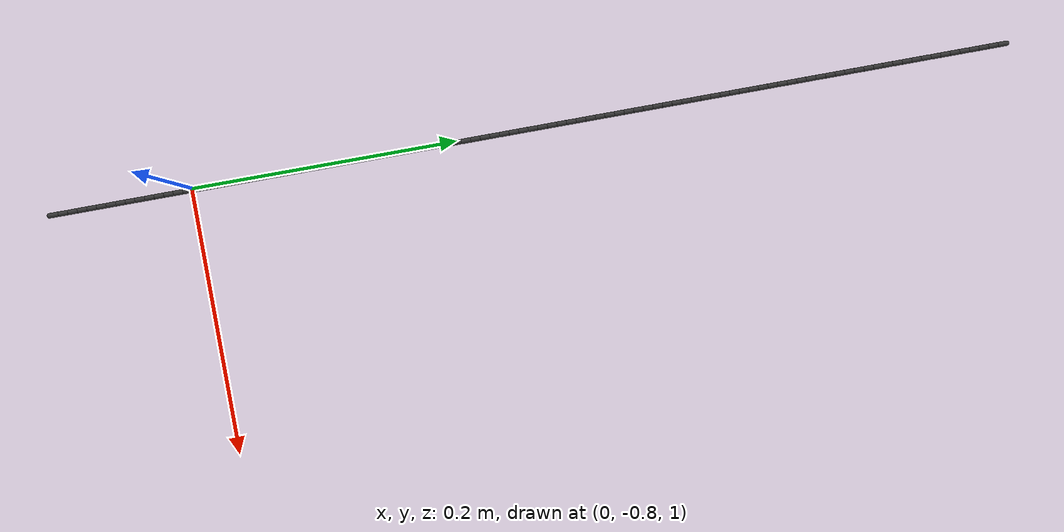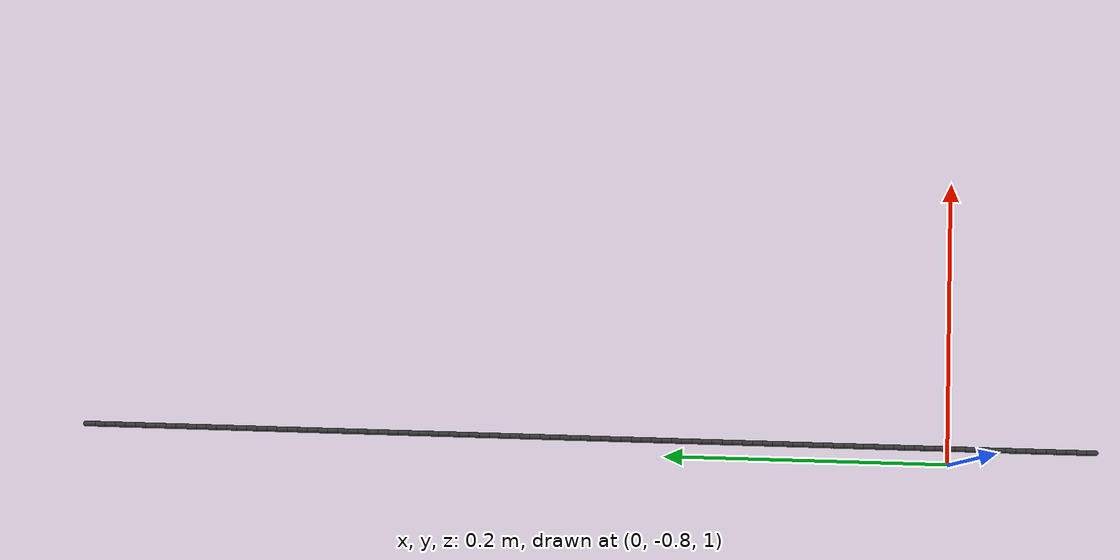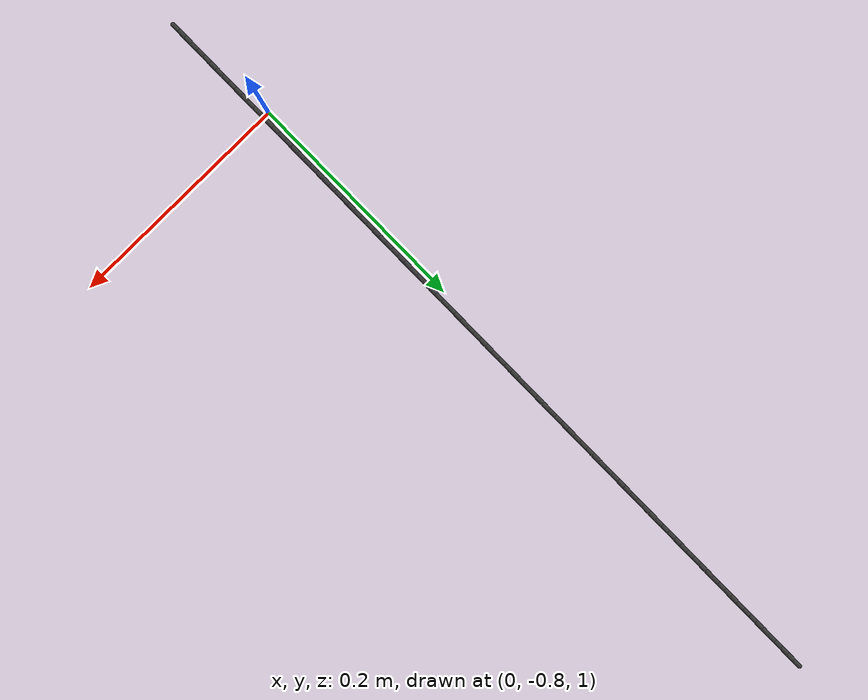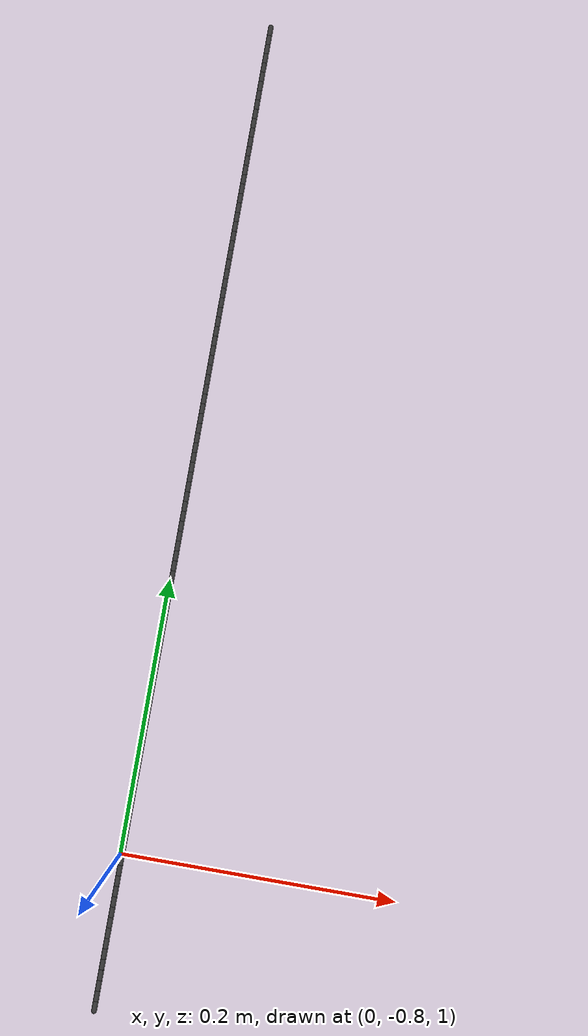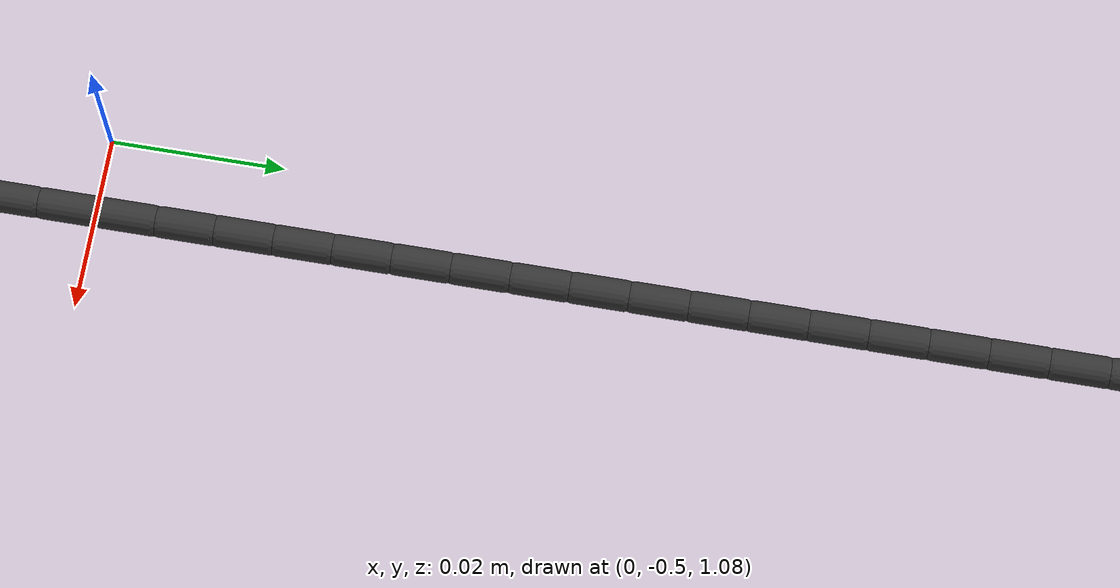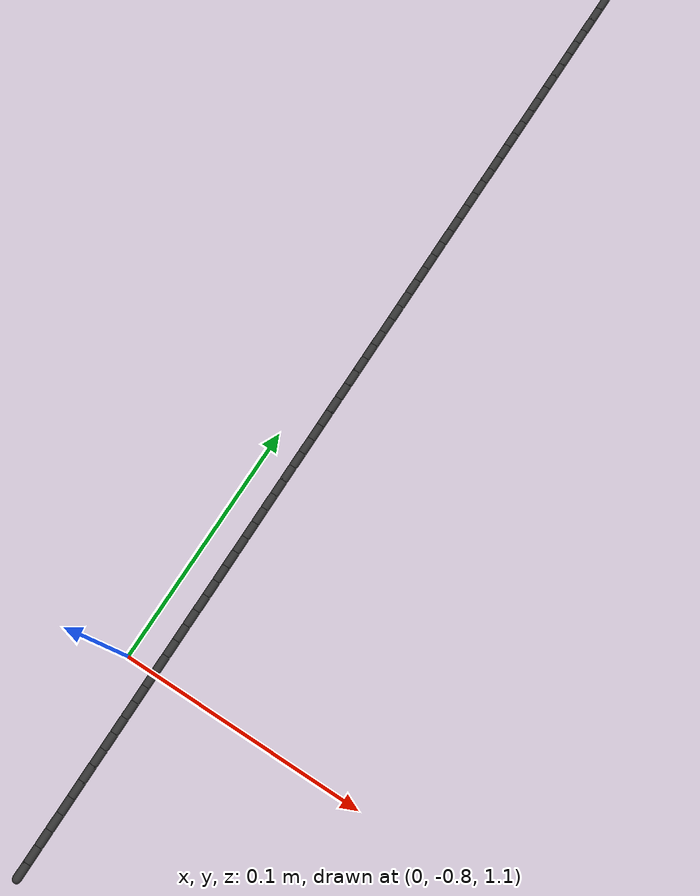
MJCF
<mujoco model="MuJoCo Model">
  <compiler angle="radian"/>
  <size njmax="500" nconmax="100"/>
  <worldbody>
    <body name="B0" pos="0.0076103 -0.88447 1.07725" quat="0.707107 0 0 0.707107">
      <inertial pos="0 0 0" quat="0.707107 0 0.707107 0" mass="7.93943e-05" diaginertia="4.66839e-10 4.66839e-10 1.28619e-10"/>
      <joint name="slider_joint" pos="0 0 0" axis="1 0 0" type="slide" limited="true" range="0 2"/>
      <geom name="G0" size="0.0018 0.003" quat="0.707107 0 0.707107 0" type="capsule" rgba="0.2 0.2 0.2 1"/>
      <body name="B1" pos="0.0068 0 0">
        <inertial pos="0 0 0" quat="0.707107 0 0.707107 0" mass="7.93943e-05" diaginertia="4.66839e-10 4.66839e-10 1.28619e-10"/>
        <joint name="J0_1" pos="-0.0034 0 0" axis="0 1 0" group="3" stiffness="0.01" armature="0.1" damping="0.005"/>
        <joint name="J1_1" pos="-0.0034 0 0" axis="0 0 1" group="3" stiffness="0.01" armature="0.1" damping="0.005"/>
        <geom name="G1" size="0.0018 0.003" quat="0.707107 0 0.707107 0" type="capsule" rgba="0.2 0.2 0.2 1"/>
        <body name="B2" pos="0.0068 0 0">
          <inertial pos="0 0 0" quat="0.707107 0 0.707107 0" mass="7.93943e-05" diaginertia="4.66839e-10 4.66839e-10 1.28619e-10"/>
          <joint name="J0_2" pos="-0.0034 0 0" axis="0 1 0" group="3" stiffness="0.01" armature="0.1" damping="0.005"/>
          <joint name="J1_2" pos="-0.0034 0 0" axis="0 0 1" group="3" stiffness="0.01" armature="0.1" damping="0.005"/>
          <geom name="G2" size="0.0018 0.003" quat="0.707107 0 0.707107 0" type="capsule" rgba="0.2 0.2 0.2 1"/>
          <body name="B3" pos="0.0068 0 0">
            <inertial pos="0 0 0" quat="0.707107 0 0.707107 0" mass="7.93943e-05" diaginertia="4.66839e-10 4.66839e-10 1.28619e-10"/>
            <joint name="J0_3" pos="-0.0034 0 0" axis="0 1 0" group="3" stiffness="0.01" armature="0.1" damping="0.005"/>
            <joint name="J1_3" pos="-0.0034 0 0" axis="0 0 1" group="3" stiffness="0.01" armature="0.1" damping="0.005"/>
            <geom name="G3" size="0.0018 0.003" quat="0.707107 0 0.707107 0" type="capsule" rgba="0.2 0.2 0.2 1"/>
            <body name="B4" pos="0.0068 0 0">
              <inertial pos="0 0 0" quat="0.707107 0 0.707107 0" mass="7.93943e-05" diaginertia="4.66839e-10 4.66839e-10 1.28619e-10"/>
              <joint name="J0_4" pos="-0.0034 0 0" axis="0 1 0" group="3" stiffness="0.01" armature="0.1" damping="0.005"/>
              <joint name="J1_4" pos="-0.0034 0 0" axis="0 0 1" group="3" stiffness="0.01" armature="0.1" damping="0.005"/>
              <geom name="G4" size="0.0018 0.003" quat="0.707107 0 0.707107 0" type="capsule" rgba="0.2 0.2 0.2 1"/>
              <body name="B5" pos="0.0068 0 0">
                <inertial pos="0 0 0" quat="0.707107 0 0.707107 0" mass="7.93943e-05" diaginertia="4.66839e-10 4.66839e-10 1.28619e-10"/>
                <joint name="J0_5" pos="-0.0034 0 0" axis="0 1 0" group="3" stiffness="0.01" armature="0.1" damping="0.005"/>
                <joint name="J1_5" pos="-0.0034 0 0" axis="0 0 1" group="3" stiffness="0.01" armature="0.1" damping="0.005"/>
                <geom name="G5" size="0.0018 0.003" quat="0.707107 0 0.707107 0" type="capsule" rgba="0.2 0.2 0.2 1"/>
                <body name="B6" pos="0.0068 0 0">
                  <inertial pos="0 0 0" quat="0.707107 0 0.707107 0" mass="7.93943e-05" diaginertia="4.66839e-10 4.66839e-10 1.28619e-10"/>
                  <joint name="J0_6" pos="-0.0034 0 0" axis="0 1 0" group="3" stiffness="0.01" armature="0.1" damping="0.005"/>
                  <joint name="J1_6" pos="-0.0034 0 0" axis="0 0 1" group="3" stiffness="0.01" armature="0.1" damping="0.005"/>
                  <geom name="G6" size="0.0018 0.003" quat="0.707107 0 0.707107 0" type="capsule" rgba="0.2 0.2 0.2 1"/>
                  <body name="B7" pos="0.0068 0 0">
                    <inertial pos="0 0 0" quat="0.707107 0 0.707107 0" mass="7.93943e-05" diaginertia="4.66839e-10 4.66839e-10 1.28619e-10"/>
                    <joint name="J0_7" pos="-0.0034 0 0" axis="0 1 0" group="3" stiffness="0.01" armature="0.1" damping="0.005"/>
                    <joint name="J1_7" pos="-0.0034 0 0" axis="0 0 1" group="3" stiffness="0.01" armature="0.1" damping="0.005"/>
                    <geom name="G7" size="0.0018 0.003" quat="0.707107 0 0.707107 0" type="capsule" rgba="0.2 0.2 0.2 1"/>
                    <body name="B8" pos="0.0068 0 0">
                      <inertial pos="0 0 0" quat="0.707107 0 0.707107 0" mass="7.93943e-05" diaginertia="4.66839e-10 4.66839e-10 1.28619e-10"/>
                      <joint name="J0_8" pos="-0.0034 0 0" axis="0 1 0" group="3" stiffness="0.01" armature="0.1" damping="0.005"/>
                      <joint name="J1_8" pos="-0.0034 0 0" axis="0 0 1" group="3" stiffness="0.01" armature="0.1" damping="0.005"/>
                      <geom name="G8" size="0.0018 0.003" quat="0.707107 0 0.707107 0" type="capsule" rgba="0.2 0.2 0.2 1"/>
                      <body name="B9" pos="0.0068 0 0">
                        <inertial pos="0 0 0" quat="0.707107 0 0.707107 0" mass="7.93943e-05" diaginertia="4.66839e-10 4.66839e-10 1.28619e-10"/>
                        <joint name="J0_9" pos="-0.0034 0 0" axis="0 1 0" group="3" stiffness="0.01" armature="0.1" damping="0.005"/>
                        <joint name="J1_9" pos="-0.0034 0 0" axis="0 0 1" group="3" stiffness="0.01" armature="0.1" damping="0.005"/>
                        <geom name="G9" size="0.0018 0.003" quat="0.707107 0 0.707107 0" type="capsule" rgba="0.2 0.2 0.2 1"/>
                        <body name="B10" pos="0.0068 0 0">
                          <inertial pos="0 0 0" quat="0.707107 0 0.707107 0" mass="7.93943e-05" diaginertia="4.66839e-10 4.66839e-10 1.28619e-10"/>
                          <joint name="J0_10" pos="-0.0034 0 0" axis="0 1 0" group="3" stiffness="0.01" armature="0.1" damping="0.005"/>
                          <joint name="J1_10" pos="-0.0034 0 0" axis="0 0 1" group="3" stiffness="0.01" armature="0.1" damping="0.005"/>
                          <geom name="G10" size="0.0018 0.003" quat="0.707107 0 0.707107 0" type="capsule" rgba="0.2 0.2 0.2 1"/>
                          <body name="B11" pos="0.0068 0 0">
                            <inertial pos="0 0 0" quat="0.707107 0 0.707107 0" mass="7.93943e-05" diaginertia="4.66839e-10 4.66839e-10 1.28619e-10"/>
                            <joint name="J0_11" pos="-0.0034 0 0" axis="0 1 0" group="3" stiffness="0.01" armature="0.1" damping="0.005"/>
                            <joint name="J1_11" pos="-0.0034 0 0" axis="0 0 1" group="3" stiffness="0.01" armature="0.1" damping="0.005"/>
                            <geom name="G11" size="0.0018 0.003" quat="0.707107 0 0.707107 0" type="capsule" rgba="0.2 0.2 0.2 1"/>
                            <body name="B12" pos="0.0068 0 0">
                              <inertial pos="0 0 0" quat="0.707107 0 0.707107 0" mass="7.93943e-05" diaginertia="4.66839e-10 4.66839e-10 1.28619e-10"/>
                              <joint name="J0_12" pos="-0.0034 0 0" axis="0 1 0" group="3" stiffness="0.01" armature="0.1" damping="0.005"/>
                              <joint name="J1_12" pos="-0.0034 0 0" axis="0 0 1" group="3" stiffness="0.01" armature="0.1" damping="0.005"/>
                              <geom name="G12" size="0.0018 0.003" quat="0.707107 0 0.707107 0" type="capsule" rgba="0.2 0.2 0.2 1"/>
                              <body name="B13" pos="0.0068 0 0">
                                <inertial pos="0 0 0" quat="0.707107 0 0.707107 0" mass="7.93943e-05" diaginertia="4.66839e-10 4.66839e-10 1.28619e-10"/>
                                <joint name="J0_13" pos="-0.0034 0 0" axis="0 1 0" group="3" stiffness="0.01" armature="0.1" damping="0.005"/>
                                <joint name="J1_13" pos="-0.0034 0 0" axis="0 0 1" group="3" stiffness="0.01" armature="0.1" damping="0.005"/>
                                <geom name="G13" size="0.0018 0.003" quat="0.707107 0 0.707107 0" type="capsule" rgba="0.2 0.2 0.2 1"/>
                                <body name="B14" pos="0.0068 0 0">
                                  <inertial pos="0 0 0" quat="0.707107 0 0.707107 0" mass="7.93943e-05" diaginertia="4.66839e-10 4.66839e-10 1.28619e-10"/>
                                  <joint name="J0_14" pos="-0.0034 0 0" axis="0 1 0" group="3" stiffness="0.01" armature="0.1" damping="0.005"/>
                                  <joint name="J1_14" pos="-0.0034 0 0" axis="0 0 1" group="3" stiffness="0.01" armature="0.1" damping="0.005"/>
                                  <geom name="G14" size="0.0018 0.003" quat="0.707107 0 0.707107 0" type="capsule" rgba="0.2 0.2 0.2 1"/>
                                  <body name="B15" pos="0.0068 0 0">
                                    <inertial pos="0 0 0" quat="0.707107 0 0.707107 0" mass="7.93943e-05" diaginertia="4.66839e-10 4.66839e-10 1.28619e-10"/>
                                    <joint name="J0_15" pos="-0.0034 0 0" axis="0 1 0" group="3" stiffness="0.01" armature="0.1" damping="0.005"/>
                                    <joint name="J1_15" pos="-0.0034 0 0" axis="0 0 1" group="3" stiffness="0.01" armature="0.1" damping="0.005"/>
                                    <geom name="G15" size="0.0018 0.003" quat="0.707107 0 0.707107 0" type="capsule" rgba="0.2 0.2 0.2 1"/>
                                    <body name="B16" pos="0.0068 0 0">
                                      <inertial pos="0 0 0" quat="0.707107 0 0.707107 0" mass="7.93943e-05" diaginertia="4.66839e-10 4.66839e-10 1.28619e-10"/>
                                      <joint name="J0_16" pos="-0.0034 0 0" axis="0 1 0" group="3" stiffness="0.01" armature="0.1" damping="0.005"/>
                                      <joint name="J1_16" pos="-0.0034 0 0" axis="0 0 1" group="3" stiffness="0.01" armature="0.1" damping="0.005"/>
                                      <geom name="G16" size="0.0018 0.003" quat="0.707107 0 0.707107 0" type="capsule" rgba="0.2 0.2 0.2 1"/>
                                      <body name="B17" pos="0.0068 0 0">
                                        <inertial pos="0 0 0" quat="0.707107 0 0.707107 0" mass="7.93943e-05" diaginertia="4.66839e-10 4.66839e-10 1.28619e-10"/>
                                        <joint name="J0_17" pos="-0.0034 0 0" axis="0 1 0" group="3" stiffness="0.01" armature="0.1" damping="0.005"/>
                                        <joint name="J1_17" pos="-0.0034 0 0" axis="0 0 1" group="3" stiffness="0.01" armature="0.1" damping="0.005"/>
                                        <geom name="G17" size="0.0018 0.003" quat="0.707107 0 0.707107 0" type="capsule" rgba="0.2 0.2 0.2 1"/>
                                        <body name="B18" pos="0.0068 0 0">
                                          <inertial pos="0 0 0" quat="0.707107 0 0.707107 0" mass="7.93943e-05" diaginertia="4.66839e-10 4.66839e-10 1.28619e-10"/>
                                          <joint name="J0_18" pos="-0.0034 0 0" axis="0 1 0" group="3" stiffness="0.01" armature="0.1" damping="0.005"/>
                                          <joint name="J1_18" pos="-0.0034 0 0" axis="0 0 1" group="3" stiffness="0.01" armature="0.1" damping="0.005"/>
                                          <geom name="G18" size="0.0018 0.003" quat="0.707107 0 0.707107 0" type="capsule" rgba="0.2 0.2 0.2 1"/>
                                          <body name="B19" pos="0.0068 0 0">
                                            <inertial pos="0 0 0" quat="0.707107 0 0.707107 0" mass="7.93943e-05" diaginertia="4.66839e-10 4.66839e-10 1.28619e-10"/>
                                            <joint name="J0_19" pos="-0.0034 0 0" axis="0 1 0" group="3" stiffness="0.01" armature="0.1" damping="0.005"/>
                                            <joint name="J1_19" pos="-0.0034 0 0" axis="0 0 1" group="3" stiffness="0.01" armature="0.1" damping="0.005"/>
                                            <geom name="G19" size="0.0018 0.003" quat="0.707107 0 0.707107 0" type="capsule" rgba="0.2 0.2 0.2 1"/>
                                            <body name="B20" pos="0.0068 0 0">
                                              <inertial pos="0 0 0" quat="0.707107 0 0.707107 0" mass="7.93943e-05" diaginertia="4.66839e-10 4.66839e-10 1.28619e-10"/>
                                              <joint name="J0_20" pos="-0.0034 0 0" axis="0 1 0" group="3" stiffness="0.01" armature="0.1" damping="0.005"/>
                                              <joint name="J1_20" pos="-0.0034 0 0" axis="0 0 1" group="3" stiffness="0.01" armature="0.1" damping="0.005"/>
                                              <geom name="G20" size="0.0018 0.003" quat="0.707107 0 0.707107 0" type="capsule" rgba="0.2 0.2 0.2 1"/>
                                              <body name="B21" pos="0.0068 0 0">
                                                <inertial pos="0 0 0" quat="0.707107 0 0.707107 0" mass="7.93943e-05" diaginertia="4.66839e-10 4.66839e-10 1.28619e-10"/>
                                                <joint name="J0_21" pos="-0.0034 0 0" axis="0 1 0" group="3" stiffness="0.01" armature="0.1" damping="0.005"/>
                                                <joint name="J1_21" pos="-0.0034 0 0" axis="0 0 1" group="3" stiffness="0.01" armature="0.1" damping="0.005"/>
                                                <geom name="G21" size="0.0018 0.003" quat="0.707107 0 0.707107 0" type="capsule" rgba="0.2 0.2 0.2 1"/>
                                                <body name="B22" pos="0.0068 0 0">
                                                  <inertial pos="0 0 0" quat="0.707107 0 0.707107 0" mass="7.93943e-05" diaginertia="4.66839e-10 4.66839e-10 1.28619e-10"/>
                                                  <joint name="J0_22" pos="-0.0034 0 0" axis="0 1 0" group="3" stiffness="0.01" armature="0.1" damping="0.005"/>
                                                  <joint name="J1_22" pos="-0.0034 0 0" axis="0 0 1" group="3" stiffness="0.01" armature="0.1" damping="0.005"/>
                                                  <geom name="G22" size="0.0018 0.003" quat="0.707107 0 0.707107 0" type="capsule" rgba="0.2 0.2 0.2 1"/>
                                                  <body name="B23" pos="0.0068 0 0">
                                                    <inertial pos="0 0 0" quat="0.707107 0 0.707107 0" mass="7.93943e-05" diaginertia="4.66839e-10 4.66839e-10 1.28619e-10"/>
                                                    <joint name="J0_23" pos="-0.0034 0 0" axis="0 1 0" group="3" stiffness="0.01" armature="0.1" damping="0.005"/>
                                                    <joint name="J1_23" pos="-0.0034 0 0" axis="0 0 1" group="3" stiffness="0.01" armature="0.1" damping="0.005"/>
                                                    <geom name="G23" size="0.0018 0.003" quat="0.707107 0 0.707107 0" type="capsule" rgba="0.2 0.2 0.2 1"/>
                                                    <body name="B24" pos="0.0068 0 0">
                                                      <inertial pos="0 0 0" quat="0.707107 0 0.707107 0" mass="7.93943e-05" diaginertia="4.66839e-10 4.66839e-10 1.28619e-10"/>
                                                      <joint name="J0_24" pos="-0.0034 0 0" axis="0 1 0" group="3" stiffness="0.01" armature="0.1" damping="0.005"/>
                                                      <joint name="J1_24" pos="-0.0034 0 0" axis="0 0 1" group="3" stiffness="0.01" armature="0.1" damping="0.005"/>
                                                      <geom name="G24" size="0.0018 0.003" quat="0.707107 0 0.707107 0" type="capsule" rgba="0.2 0.2 0.2 1"/>
                                                      <body name="B25" pos="0.0068 0 0">
                                                        <inertial pos="0 0 0" quat="0.707107 0 0.707107 0" mass="7.93943e-05" diaginertia="4.66839e-10 4.66839e-10 1.28619e-10"/>
                                                        <joint name="J0_25" pos="-0.0034 0 0" axis="0 1 0" group="3" stiffness="0.01" armature="0.1" damping="0.005"/>
                                                        <joint name="J1_25" pos="-0.0034 0 0" axis="0 0 1" group="3" stiffness="0.01" armature="0.1" damping="0.005"/>
                                                        <geom name="G25" size="0.0018 0.003" quat="0.707107 0 0.707107 0" type="capsule" rgba="0.2 0.2 0.2 1"/>
                                                        <body name="B26" pos="0.0068 0 0">
                                                          <inertial pos="0 0 0" quat="0.707107 0 0.707107 0" mass="7.93943e-05" diaginertia="4.66839e-10 4.66839e-10 1.28619e-10"/>
                                                          <joint name="J0_26" pos="-0.0034 0 0" axis="0 1 0" group="3" stiffness="0.01" armature="0.1" damping="0.005"/>
                                                          <joint name="J1_26" pos="-0.0034 0 0" axis="0 0 1" group="3" stiffness="0.01" armature="0.1" damping="0.005"/>
                                                          <geom name="G26" size="0.0018 0.003" quat="0.707107 0 0.707107 0" type="capsule" rgba="0.2 0.2 0.2 1"/>
                                                          <body name="B27" pos="0.0068 0 0">
                                                            <inertial pos="0 0 0" quat="0.707107 0 0.707107 0" mass="7.93943e-05" diaginertia="4.66839e-10 4.66839e-10 1.28619e-10"/>
                                                            <joint name="J0_27" pos="-0.0034 0 0" axis="0 1 0" group="3" stiffness="0.01" armature="0.1" damping="0.005"/>
                                                            <joint name="J1_27" pos="-0.0034 0 0" axis="0 0 1" group="3" stiffness="0.01" armature="0.1" damping="0.005"/>
                                                            <geom name="G27" size="0.0018 0.003" quat="0.707107 0 0.707107 0" type="capsule" rgba="0.2 0.2 0.2 1"/>
                                                            <body name="B28" pos="0.0068 0 0">
                                                              <inertial pos="0 0 0" quat="0.707107 0 0.707107 0" mass="7.93943e-05" diaginertia="4.66839e-10 4.66839e-10 1.28619e-10"/>
                                                              <joint name="J0_28" pos="-0.0034 0 0" axis="0 1 0" group="3" stiffness="0.01" armature="0.1" damping="0.005"/>
                                                              <joint name="J1_28" pos="-0.0034 0 0" axis="0 0 1" group="3" stiffness="0.01" armature="0.1" damping="0.005"/>
                                                              <geom name="G28" size="0.0018 0.003" quat="0.707107 0 0.707107 0" type="capsule" rgba="0.2 0.2 0.2 1"/>
                                                              <body name="B29" pos="0.0068 0 0">
                                                                <inertial pos="0 0 0" quat="0.707107 0 0.707107 0" mass="7.93943e-05" diaginertia="4.66839e-10 4.66839e-10 1.28619e-10"/>
                                                                <joint name="J0_29" pos="-0.0034 0 0" axis="0 1 0" group="3" stiffness="0.01" armature="0.1" damping="0.005"/>
                                                                <joint name="J1_29" pos="-0.0034 0 0" axis="0 0 1" group="3" stiffness="0.01" armature="0.1" damping="0.005"/>
                                                                <geom name="G29" size="0.0018 0.003" quat="0.707107 0 0.707107 0" type="capsule" rgba="0.2 0.2 0.2 1"/>
                                                                <body name="B30" pos="0.0068 0 0">
                                                                  <inertial pos="0 0 0" quat="0.707107 0 0.707107 0" mass="7.93943e-05" diaginertia="4.66839e-10 4.66839e-10 1.28619e-10"/>
                                                                  <joint name="J0_30" pos="-0.0034 0 0" axis="0 1 0" group="3" stiffness="0.01" armature="0.1" damping="0.005"/>
                                                                  <joint name="J1_30" pos="-0.0034 0 0" axis="0 0 1" group="3" stiffness="0.01" armature="0.1" damping="0.005"/>
                                                                  <geom name="G30" size="0.0018 0.003" quat="0.707107 0 0.707107 0" type="capsule" rgba="0.2 0.2 0.2 1"/>
                                                                  <body name="B31" pos="0.0068 0 0">
                                                                    <inertial pos="0 0 0" quat="0.707107 0 0.707107 0" mass="7.93943e-05" diaginertia="4.66839e-10 4.66839e-10 1.28619e-10"/>
                                                                    <joint name="J0_31" pos="-0.0034 0 0" axis="0 1 0" group="3" stiffness="0.01" armature="0.1" damping="0.005"/>
                                                                    <joint name="J1_31" pos="-0.0034 0 0" axis="0 0 1" group="3" stiffness="0.01" armature="0.1" damping="0.005"/>
                                                                    <geom name="G31" size="0.0018 0.003" quat="0.707107 0 0.707107 0" type="capsule" rgba="0.2 0.2 0.2 1"/>
                                                                    <body name="B32" pos="0.0068 0 0">
                                                                      <inertial pos="0 0 0" quat="0.707107 0 0.707107 0" mass="7.93943e-05" diaginertia="4.66839e-10 4.66839e-10 1.28619e-10"/>
                                                                      <joint name="J0_32" pos="-0.0034 0 0" axis="0 1 0" group="3" stiffness="0.01" armature="0.1" damping="0.005"/>
                                                                      <joint name="J1_32" pos="-0.0034 0 0" axis="0 0 1" group="3" stiffness="0.01" armature="0.1" damping="0.005"/>
                                                                      <geom name="G32" size="0.0018 0.003" quat="0.707107 0 0.707107 0" type="capsule" rgba="0.2 0.2 0.2 1"/>
                                                                      <body name="B33" pos="0.0068 0 0">
                                                                        <inertial pos="0 0 0" quat="0.707107 0 0.707107 0" mass="7.93943e-05" diaginertia="4.66839e-10 4.66839e-10 1.28619e-10"/>
                                                                        <joint name="J0_33" pos="-0.0034 0 0" axis="0 1 0" group="3" stiffness="0.01" armature="0.1" damping="0.005"/>
                                                                        <joint name="J1_33" pos="-0.0034 0 0" axis="0 0 1" group="3" stiffness="0.01" armature="0.1" damping="0.005"/>
                                                                        <geom name="G33" size="0.0018 0.003" quat="0.707107 0 0.707107 0" type="capsule" rgba="0.2 0.2 0.2 1"/>
                                                                        <body name="B34" pos="0.0068 0 0">
                                                                          <inertial pos="0 0 0" quat="0.707107 0 0.707107 0" mass="7.93943e-05" diaginertia="4.66839e-10 4.66839e-10 1.28619e-10"/>
                                                                          <joint name="J0_34" pos="-0.0034 0 0" axis="0 1 0" group="3" stiffness="0.01" armature="0.1" damping="0.005"/>
                                                                          <joint name="J1_34" pos="-0.0034 0 0" axis="0 0 1" group="3" stiffness="0.01" armature="0.1" damping="0.005"/>
                                                                          <geom name="G34" size="0.0018 0.003" quat="0.707107 0 0.707107 0" type="capsule" rgba="0.2 0.2 0.2 1"/>
                                                                          <body name="B35" pos="0.0068 0 0">
                                                                            <inertial pos="0 0 0" quat="0.707107 0 0.707107 0" mass="7.93943e-05" diaginertia="4.66839e-10 4.66839e-10 1.28619e-10"/>
                                                                            <joint name="J0_35" pos="-0.0034 0 0" axis="0 1 0" group="3" stiffness="0.01" armature="0.1" damping="0.005"/>
                                                                            <joint name="J1_35" pos="-0.0034 0 0" axis="0 0 1" group="3" stiffness="0.01" armature="0.1" damping="0.005"/>
                                                                            <geom name="G35" size="0.0018 0.003" quat="0.707107 0 0.707107 0" type="capsule" rgba="0.2 0.2 0.2 1"/>
                                                                            <body name="B36" pos="0.0068 0 0">
                                                                              <inertial pos="0 0 0" quat="0.707107 0 0.707107 0" mass="7.93943e-05" diaginertia="4.66839e-10 4.66839e-10 1.28619e-10"/>
                                                                              <joint name="J0_36" pos="-0.0034 0 0" axis="0 1 0" group="3" stiffness="0.01" armature="0.1" damping="0.005"/>
                                                                              <joint name="J1_36" pos="-0.0034 0 0" axis="0 0 1" group="3" stiffness="0.01" armature="0.1" damping="0.005"/>
                                                                              <geom name="G36" size="0.0018 0.003" quat="0.707107 0 0.707107 0" type="capsule" rgba="0.2 0.2 0.2 1"/>
                                                                              <body name="B37" pos="0.0068 0 0">
                                                                                <inertial pos="0 0 0" quat="0.707107 0 0.707107 0" mass="7.93943e-05" diaginertia="4.66839e-10 4.66839e-10 1.28619e-10"/>
                                                                                <joint name="J0_37" pos="-0.0034 0 0" axis="0 1 0" group="3" stiffness="0.01" armature="0.1" damping="0.005"/>
                                                                                <joint name="J1_37" pos="-0.0034 0 0" axis="0 0 1" group="3" stiffness="0.01" armature="0.1" damping="0.005"/>
                                                                                <geom name="G37" size="0.0018 0.003" quat="0.707107 0 0.707107 0" type="capsule" rgba="0.2 0.2 0.2 1"/>
                                                                                <body name="B38" pos="0.0068 0 0">
                                                                                  <inertial pos="0 0 0" quat="0.707107 0 0.707107 0" mass="7.93943e-05" diaginertia="4.66839e-10 4.66839e-10 1.28619e-10"/>
                                                                                  <joint name="J0_38" pos="-0.0034 0 0" axis="0 1 0" group="3" stiffness="0.01" armature="0.1" damping="0.005"/>
                                                                                  <joint name="J1_38" pos="-0.0034 0 0" axis="0 0 1" group="3" stiffness="0.01" armature="0.1" damping="0.005"/>
                                                                                  <geom name="G38" size="0.0018 0.003" quat="0.707107 0 0.707107 0" type="capsule" rgba="0.2 0.2 0.2 1"/>
                                                                                  <body name="B39" pos="0.0068 0 0">
                                                                                    <inertial pos="0 0 0" quat="0.707107 0 0.707107 0" mass="7.93943e-05" diaginertia="4.66839e-10 4.66839e-10 1.28619e-10"/>
                                                                                    <joint name="J0_39" pos="-0.0034 0 0" axis="0 1 0" group="3" stiffness="0.01" armature="0.1" damping="0.005"/>
                                                                                    <joint name="J1_39" pos="-0.0034 0 0" axis="0 0 1" group="3" stiffness="0.01" armature="0.1" damping="0.005"/>
                                                                                    <geom name="G39" size="0.0018 0.003" quat="0.707107 0 0.707107 0" type="capsule" rgba="0.2 0.2 0.2 1"/>
                                                                                    <body name="B40" pos="0.0068 0 0">
                                                                                      <inertial pos="0 0 0" quat="0.707107 0 0.707107 0" mass="7.93943e-05" diaginertia="4.66839e-10 4.66839e-10 1.28619e-10"/>
                                                                                      <joint name="J0_40" pos="-0.0034 0 0" axis="0 1 0" group="3" stiffness="0.01" armature="0.1" damping="0.005"/>
                                                                                      <joint name="J1_40" pos="-0.0034 0 0" axis="0 0 1" group="3" stiffness="0.01" armature="0.1" damping="0.005"/>
                                                                                      <geom name="G40" size="0.0018 0.003" quat="0.707107 0 0.707107 0" type="capsule" rgba="0.2 0.2 0.2 1"/>
                                                                                      <body name="B41" pos="0.0068 0 0">
                                                                                        <inertial pos="0 0 0" quat="0.707107 0 0.707107 0" mass="7.93943e-05" diaginertia="4.66839e-10 4.66839e-10 1.28619e-10"/>
                                                                                        <joint name="J0_41" pos="-0.0034 0 0" axis="0 1 0" group="3" stiffness="0.01" armature="0.1" damping="0.005"/>
                                                                                        <joint name="J1_41" pos="-0.0034 0 0" axis="0 0 1" group="3" stiffness="0.01" armature="0.1" damping="0.005"/>
                                                                                        <geom name="G41" size="0.0018 0.003" quat="0.707107 0 0.707107 0" type="capsule" rgba="0.2 0.2 0.2 1"/>
                                                                                        <body name="B42" pos="0.0068 0 0">
                                                                                          <inertial pos="0 0 0" quat="0.707107 0 0.707107 0" mass="7.93943e-05" diaginertia="4.66839e-10 4.66839e-10 1.28619e-10"/>
                                                                                          <joint name="J0_42" pos="-0.0034 0 0" axis="0 1 0" group="3" stiffness="0.01" armature="0.1" damping="0.005"/>
                                                                                          <joint name="J1_42" pos="-0.0034 0 0" axis="0 0 1" group="3" stiffness="0.01" armature="0.1" damping="0.005"/>
                                                                                          <geom name="G42" size="0.0018 0.003" quat="0.707107 0 0.707107 0" type="capsule" rgba="0.2 0.2 0.2 1"/>
                                                                                          <body name="B43" pos="0.0068 0 0">
                                                                                            <inertial pos="0 0 0" quat="0.707107 0 0.707107 0" mass="7.93943e-05" diaginertia="4.66839e-10 4.66839e-10 1.28619e-10"/>
                                                                                            <joint name="J0_43" pos="-0.0034 0 0" axis="0 1 0" group="3" stiffness="0.01" armature="0.1" damping="0.005"/>
                                                                                            <joint name="J1_43" pos="-0.0034 0 0" axis="0 0 1" group="3" stiffness="0.01" armature="0.1" damping="0.005"/>
                                                                                            <geom name="G43" size="0.0018 0.003" quat="0.707107 0 0.707107 0" type="capsule" rgba="0.2 0.2 0.2 1"/>
                                                                                            <body name="B44" pos="0.0068 0 0">
                                                                                              <inertial pos="0 0 0" quat="0.707107 0 0.707107 0" mass="7.93943e-05" diaginertia="4.66839e-10 4.66839e-10 1.28619e-10"/>
                                                                                              <joint name="J0_44" pos="-0.0034 0 0" axis="0 1 0" group="3" stiffness="0.01" armature="0.1" damping="0.005"/>
                                                                                              <joint name="J1_44" pos="-0.0034 0 0" axis="0 0 1" group="3" stiffness="0.01" armature="0.1" damping="0.005"/>
                                                                                              <geom name="G44" size="0.0018 0.003" quat="0.707107 0 0.707107 0" type="capsule" rgba="0.2 0.2 0.2 1"/>
                                                                                              <body name="B45" pos="0.0068 0 0">
                                                                                                <inertial pos="0 0 0" quat="0.707107 0 0.707107 0" mass="7.93943e-05" diaginertia="4.66839e-10 4.66839e-10 1.28619e-10"/>
                                                                                                <joint name="J0_45" pos="-0.0034 0 0" axis="0 1 0" group="3" stiffness="0.01" armature="0.1" damping="0.005"/>
                                                                                                <joint name="J1_45" pos="-0.0034 0 0" axis="0 0 1" group="3" stiffness="0.01" armature="0.1" damping="0.005"/>
                                                                                                <geom name="G45" size="0.0018 0.003" quat="0.707107 0 0.707107 0" type="capsule" rgba="0.2 0.2 0.2 1"/>
                                                                                                <body name="B46" pos="0.0068 0 0">
                                                                                                  <inertial pos="0 0 0" quat="0.707107 0 0.707107 0" mass="7.93943e-05" diaginertia="4.66839e-10 4.66839e-10 1.28619e-10"/>
                                                                                                  <joint name="J0_46" pos="-0.0034 0 0" axis="0 1 0" group="3" stiffness="0.01" armature="0.1" damping="0.005"/>
                                                                                                  <joint name="J1_46" pos="-0.0034 0 0" axis="0 0 1" group="3" stiffness="0.01" armature="0.1" damping="0.005"/>
                                                                                                  <geom name="G46" size="0.0018 0.003" quat="0.707107 0 0.707107 0" type="capsule" rgba="0.2 0.2 0.2 1"/>
                                                                                                  <body name="B47" pos="0.0068 0 0">
                                                                                                    <inertial pos="0 0 0" quat="0.707107 0 0.707107 0" mass="7.93943e-05" diaginertia="4.66839e-10 4.66839e-10 1.28619e-10"/>
                                                                                                    <joint name="J0_47" pos="-0.0034 0 0" axis="0 1 0" group="3" stiffness="0.01" armature="0.1" damping="0.005"/>
                                                                                                    <joint name="J1_47" pos="-0.0034 0 0" axis="0 0 1" group="3" stiffness="0.01" armature="0.1" damping="0.005"/>
                                                                                                    <geom name="G47" size="0.0018 0.003" quat="0.707107 0 0.707107 0" type="capsule" rgba="0.2 0.2 0.2 1"/>
                                                                                                    <body name="B48" pos="0.0068 0 0">
                                                                                                      <inertial pos="0 0 0" quat="0.707107 0 0.707107 0" mass="7.93943e-05" diaginertia="4.66839e-10 4.66839e-10 1.28619e-10"/>
                                                                                                      <joint name="J0_48" pos="-0.0034 0 0" axis="0 1 0" group="3" stiffness="0.01" armature="0.1" damping="0.005"/>
                                                                                                      <joint name="J1_48" pos="-0.0034 0 0" axis="0 0 1" group="3" stiffness="0.01" armature="0.1" damping="0.005"/>
                                                                                                      <geom name="G48" size="0.0018 0.003" quat="0.707107 0 0.707107 0" type="capsule" rgba="0.2 0.2 0.2 1"/>
                                                                                                      <body name="B49" pos="0.0068 0 0">
                                                                                                        <inertial pos="0 0 0" quat="0.707107 0 0.707107 0" mass="7.93943e-05" diaginertia="4.66839e-10 4.66839e-10 1.28619e-10"/>
                                                                                                        <joint name="J0_49" pos="-0.0034 0 0" axis="0 1 0" group="3" stiffness="0.01" armature="0.1" damping="0.005"/>
                                                                                                        <joint name="J1_49" pos="-0.0034 0 0" axis="0 0 1" group="3" stiffness="0.01" armature="0.1" damping="0.005"/>
                                                                                                        <geom name="G49" size="0.0018 0.003" quat="0.707107 0 0.707107 0" type="capsule" rgba="0.2 0.2 0.2 1"/>
                                                                                                        <body name="B50" pos="0.0068 0 0">
                                                                                                          <inertial pos="0 0 0" quat="0.707107 0 0.707107 0" mass="7.93943e-05" diaginertia="4.66839e-10 4.66839e-10 1.28619e-10"/>
                                                                                                          <joint name="J0_50" pos="-0.0034 0 0" axis="0 1 0" group="3" stiffness="0.01" armature="0.1" damping="0.005"/>
                                                                                                          <joint name="J1_50" pos="-0.0034 0 0" axis="0 0 1" group="3" stiffness="0.01" armature="0.1" damping="0.005"/>
                                                                                                          <geom name="G50" size="0.0018 0.003" quat="0.707107 0 0.707107 0" type="capsule" rgba="0.2 0.2 0.2 1"/>
                                                                                                          <body name="B51" pos="0.0068 0 0">
                                                                                                            <inertial pos="0 0 0" quat="0.707107 0 0.707107 0" mass="7.93943e-05" diaginertia="4.66839e-10 4.66839e-10 1.28619e-10"/>
                                                                                                            <joint name="J0_51" pos="-0.0034 0 0" axis="0 1 0" group="3" stiffness="0.01" armature="0.1" damping="0.005"/>
                                                                                                            <joint name="J1_51" pos="-0.0034 0 0" axis="0 0 1" group="3" stiffness="0.01" armature="0.1" damping="0.005"/>
                                                                                                            <geom name="G51" size="0.0018 0.003" quat="0.707107 0 0.707107 0" type="capsule" rgba="0.2 0.2 0.2 1"/>
                                                                                                            <body name="B52" pos="0.0068 0 0">
                                                                                                              <inertial pos="0 0 0" quat="0.707107 0 0.707107 0" mass="7.93943e-05" diaginertia="4.66839e-10 4.66839e-10 1.28619e-10"/>
                                                                                                              <joint name="J0_52" pos="-0.0034 0 0" axis="0 1 0" group="3" stiffness="0.01" armature="0.1" damping="0.005"/>
                                                                                                              <joint name="J1_52" pos="-0.0034 0 0" axis="0 0 1" group="3" stiffness="0.01" armature="0.1" damping="0.005"/>
                                                                                                              <geom name="G52" size="0.0018 0.003" quat="0.707107 0 0.707107 0" type="capsule" rgba="0.2 0.2 0.2 1"/>
                                                                                                              <body name="B53" pos="0.0068 0 0">
                                                                                                                <inertial pos="0 0 0" quat="0.707107 0 0.707107 0" mass="7.93943e-05" diaginertia="4.66839e-10 4.66839e-10 1.28619e-10"/>
                                                                                                                <joint name="J0_53" pos="-0.0034 0 0" axis="0 1 0" group="3" stiffness="0.01" armature="0.1" damping="0.005"/>
                                                                                                                <joint name="J1_53" pos="-0.0034 0 0" axis="0 0 1" group="3" stiffness="0.01" armature="0.1" damping="0.005"/>
                                                                                                                <geom name="G53" size="0.0018 0.003" quat="0.707107 0 0.707107 0" type="capsule" rgba="0.2 0.2 0.2 1"/>
                                                                                                                <body name="B54" pos="0.0068 0 0">
                                                                                                                  <inertial pos="0 0 0" quat="0.707107 0 0.707107 0" mass="7.93943e-05" diaginertia="4.66839e-10 4.66839e-10 1.28619e-10"/>
                                                                                                                  <joint name="J0_54" pos="-0.0034 0 0" axis="0 1 0" group="3" stiffness="0.01" armature="0.1" damping="0.005"/>
                                                                                                                  <joint name="J1_54" pos="-0.0034 0 0" axis="0 0 1" group="3" stiffness="0.01" armature="0.1" damping="0.005"/>
                                                                                                                  <geom name="G54" size="0.0018 0.003" quat="0.707107 0 0.707107 0" type="capsule" rgba="0.2 0.2 0.2 1"/>
                                                                                                                  <body name="B55" pos="0.0068 0 0">
                                                                                                                    <inertial pos="0 0 0" quat="0.707107 0 0.707107 0" mass="7.93943e-05" diaginertia="4.66839e-10 4.66839e-10 1.28619e-10"/>
                                                                                                                    <joint name="J0_55" pos="-0.0034 0 0" axis="0 1 0" group="3" stiffness="0.01" armature="0.1" damping="0.005"/>
                                                                                                                    <joint name="J1_55" pos="-0.0034 0 0" axis="0 0 1" group="3" stiffness="0.01" armature="0.1" damping="0.005"/>
                                                                                                                    <geom name="G55" size="0.0018 0.003" quat="0.707107 0 0.707107 0" type="capsule" rgba="0.2 0.2 0.2 1"/>
                                                                                                                    <body name="B56" pos="0.0068 0 0">
                                                                                                                      <inertial pos="0 0 0" quat="0.707107 0 0.707107 0" mass="7.93943e-05" diaginertia="4.66839e-10 4.66839e-10 1.28619e-10"/>
                                                                                                                      <joint name="J0_56" pos="-0.0034 0 0" axis="0 1 0" group="3" stiffness="0.01" armature="0.1" damping="0.005"/>
                                                                                                                      <joint name="J1_56" pos="-0.0034 0 0" axis="0 0 1" group="3" stiffness="0.01" armature="0.1" damping="0.005"/>
                                                                                                                      <geom name="G56" size="0.0018 0.003" quat="0.707107 0 0.707107 0" type="capsule" rgba="0.2 0.2 0.2 1"/>
                                                                                                                      <body name="B57" pos="0.0068 0 0">
                                                                                                                        <inertial pos="0 0 0" quat="0.707107 0 0.707107 0" mass="7.93943e-05" diaginertia="4.66839e-10 4.66839e-10 1.28619e-10"/>
                                                                                                                        <joint name="J0_57" pos="-0.0034 0 0" axis="0 1 0" group="3" stiffness="0.01" armature="0.1" damping="0.005"/>
                                                                                                                        <joint name="J1_57" pos="-0.0034 0 0" axis="0 0 1" group="3" stiffness="0.01" armature="0.1" damping="0.005"/>
                                                                                                                        <geom name="G57" size="0.0018 0.003" quat="0.707107 0 0.707107 0" type="capsule" rgba="0.2 0.2 0.2 1"/>
                                                                                                                        <body name="B58" pos="0.0068 0 0">
                                                                                                                          <inertial pos="0 0 0" quat="0.707107 0 0.707107 0" mass="7.93943e-05" diaginertia="4.66839e-10 4.66839e-10 1.28619e-10"/>
                                                                                                                          <joint name="J0_58" pos="-0.0034 0 0" axis="0 1 0" group="3" stiffness="0.01" armature="0.1" damping="0.005"/>
                                                                                                                          <joint name="J1_58" pos="-0.0034 0 0" axis="0 0 1" group="3" stiffness="0.01" armature="0.1" damping="0.005"/>
                                                                                                                          <geom name="G58" size="0.0018 0.003" quat="0.707107 0 0.707107 0" type="capsule" rgba="0.2 0.2 0.2 1"/>
                                                                                                                          <body name="B59" pos="0.0068 0 0">
                                                                                                                            <inertial pos="0 0 0" quat="0.707107 0 0.707107 0" mass="7.93943e-05" diaginertia="4.66839e-10 4.66839e-10 1.28619e-10"/>
                                                                                                                            <joint name="J0_59" pos="-0.0034 0 0" axis="0 1 0" group="3" stiffness="0.01" armature="0.1" damping="0.005"/>
                                                                                                                            <joint name="J1_59" pos="-0.0034 0 0" axis="0 0 1" group="3" stiffness="0.01" armature="0.1" damping="0.005"/>
                                                                                                                            <geom name="G59" size="0.0018 0.003" quat="0.707107 0 0.707107 0" type="capsule" rgba="0.2 0.2 0.2 1"/>
                                                                                                                            <body name="B60" pos="0.0068 0 0">
                                                                                                                              <inertial pos="0 0 0" quat="0.707107 0 0.707107 0" mass="7.93943e-05" diaginertia="4.66839e-10 4.66839e-10 1.28619e-10"/>
                                                                                                                              <joint name="J0_60" pos="-0.0034 0 0" axis="0 1 0" group="3" stiffness="0.01" armature="0.1" damping="0.005"/>
                                                                                                                              <joint name="J1_60" pos="-0.0034 0 0" axis="0 0 1" group="3" stiffness="0.01" armature="0.1" damping="0.005"/>
                                                                                                                              <geom name="G60" size="0.0018 0.003" quat="0.707107 0 0.707107 0" type="capsule" rgba="0.2 0.2 0.2 1"/>
                                                                                                                              <body name="B61" pos="0.0068 0 0">
                                                                                                                                <inertial pos="0 0 0" quat="0.707107 0 0.707107 0" mass="7.93943e-05" diaginertia="4.66839e-10 4.66839e-10 1.28619e-10"/>
                                                                                                                                <joint name="J0_61" pos="-0.0034 0 0" axis="0 1 0" group="3" stiffness="0.01" armature="0.1" damping="0.005"/>
                                                                                                                                <joint name="J1_61" pos="-0.0034 0 0" axis="0 0 1" group="3" stiffness="0.01" armature="0.1" damping="0.005"/>
                                                                                                                                <geom name="G61" size="0.0018 0.003" quat="0.707107 0 0.707107 0" type="capsule" rgba="0.2 0.2 0.2 1"/>
                                                                                                                                <body name="B62" pos="0.0068 0 0">
                                                                                                                                  <inertial pos="0 0 0" quat="0.707107 0 0.707107 0" mass="7.93943e-05" diaginertia="4.66839e-10 4.66839e-10 1.28619e-10"/>
                                                                                                                                  <joint name="J0_62" pos="-0.0034 0 0" axis="0 1 0" group="3" stiffness="0.01" armature="0.1" damping="0.005"/>
                                                                                                                                  <joint name="J1_62" pos="-0.0034 0 0" axis="0 0 1" group="3" stiffness="0.01" armature="0.1" damping="0.005"/>
                                                                                                                                  <geom name="G62" size="0.0018 0.003" quat="0.707107 0 0.707107 0" type="capsule" rgba="0.2 0.2 0.2 1"/>
                                                                                                                                  <body name="B63" pos="0.0068 0 0">
                                                                                                                                    <inertial pos="0 0 0" quat="0.707107 0 0.707107 0" mass="7.93943e-05" diaginertia="4.66839e-10 4.66839e-10 1.28619e-10"/>
                                                                                                                                    <joint name="J0_63" pos="-0.0034 0 0" axis="0 1 0" group="3" stiffness="0.01" armature="0.1" damping="0.005"/>
                                                                                                                                    <joint name="J1_63" pos="-0.0034 0 0" axis="0 0 1" group="3" stiffness="0.01" armature="0.1" damping="0.005"/>
                                                                                                                                    <geom name="G63" size="0.0018 0.003" quat="0.707107 0 0.707107 0" type="capsule" rgba="0.2 0.2 0.2 1"/>
                                                                                                                                    <body name="B64" pos="0.0068 0 0">
                                                                                                                                      <inertial pos="0 0 0" quat="0.707107 0 0.707107 0" mass="7.93943e-05" diaginertia="4.66839e-10 4.66839e-10 1.28619e-10"/>
                                                                                                                                      <joint name="J0_64" pos="-0.0034 0 0" axis="0 1 0" group="3" stiffness="0.01" armature="0.1" damping="0.005"/>
                                                                                                                                      <joint name="J1_64" pos="-0.0034 0 0" axis="0 0 1" group="3" stiffness="0.01" armature="0.1" damping="0.005"/>
                                                                                                                                      <geom name="G64" size="0.0018 0.003" quat="0.707107 0 0.707107 0" type="capsule" rgba="0.2 0.2 0.2 1"/>
                                                                                                                                      <body name="B65" pos="0.0068 0 0">
                                                                                                                                        <inertial pos="0 0 0" quat="0.707107 0 0.707107 0" mass="7.93943e-05" diaginertia="4.66839e-10 4.66839e-10 1.28619e-10"/>
                                                                                                                                        <joint name="J0_65" pos="-0.0034 0 0" axis="0 1 0" group="3" stiffness="0.01" armature="0.1" damping="0.005"/>
                                                                                                                                        <joint name="J1_65" pos="-0.0034 0 0" axis="0 0 1" group="3" stiffness="0.01" armature="0.1" damping="0.005"/>
                                                                                                                                        <geom name="G65" size="0.0018 0.003" quat="0.707107 0 0.707107 0" type="capsule" rgba="0.2 0.2 0.2 1"/>
                                                                                                                                        <body name="B66" pos="0.0068 0 0">
                                                                                                                                          <inertial pos="0 0 0" quat="0.707107 0 0.707107 0" mass="7.93943e-05" diaginertia="4.66839e-10 4.66839e-10 1.28619e-10"/>
                                                                                                                                          <joint name="J0_66" pos="-0.0034 0 0" axis="0 1 0" group="3" stiffness="0.01" armature="0.1" damping="0.005"/>
                                                                                                                                          <joint name="J1_66" pos="-0.0034 0 0" axis="0 0 1" group="3" stiffness="0.01" armature="0.1" damping="0.005"/>
                                                                                                                                          <geom name="G66" size="0.0018 0.003" quat="0.707107 0 0.707107 0" type="capsule" rgba="0.2 0.2 0.2 1"/>
                                                                                                                                          <body name="B67" pos="0.0068 0 0">
                                                                                                                                            <inertial pos="0 0 0" quat="0.707107 0 0.707107 0" mass="7.93943e-05" diaginertia="4.66839e-10 4.66839e-10 1.28619e-10"/>
                                                                                                                                            <joint name="J0_67" pos="-0.0034 0 0" axis="0 1 0" group="3" stiffness="0.01" armature="0.1" damping="0.005"/>
                                                                                                                                            <joint name="J1_67" pos="-0.0034 0 0" axis="0 0 1" group="3" stiffness="0.01" armature="0.1" damping="0.005"/>
                                                                                                                                            <geom name="G67" size="0.0018 0.003" quat="0.707107 0 0.707107 0" type="capsule" rgba="0.2 0.2 0.2 1"/>
                                                                                                                                            <body name="B68" pos="0.0068 0 0">
                                                                                                                                              <inertial pos="0 0 0" quat="0.707107 0 0.707107 0" mass="7.93943e-05" diaginertia="4.66839e-10 4.66839e-10 1.28619e-10"/>
                                                                                                                                              <joint name="J0_68" pos="-0.0034 0 0" axis="0 1 0" group="3" stiffness="0.01" armature="0.1" damping="0.005"/>
                                                                                                                                              <joint name="J1_68" pos="-0.0034 0 0" axis="0 0 1" group="3" stiffness="0.01" armature="0.1" damping="0.005"/>
                                                                                                                                              <geom name="G68" size="0.0018 0.003" quat="0.707107 0 0.707107 0" type="capsule" rgba="0.2 0.2 0.2 1"/>
                                                                                                                                              <body name="B69" pos="0.0068 0 0">
                                                                                                                                                <inertial pos="0 0 0" quat="0.707107 0 0.707107 0" mass="7.93943e-05" diaginertia="4.66839e-10 4.66839e-10 1.28619e-10"/>
                                                                                                                                                <joint name="J0_69" pos="-0.0034 0 0" axis="0 1 0" group="3" stiffness="0.01" armature="0.1" damping="0.005"/>
                                                                                                                                                <joint name="J1_69" pos="-0.0034 0 0" axis="0 0 1" group="3" stiffness="0.01" armature="0.1" damping="0.005"/>
                                                                                                                                                <geom name="G69" size="0.0018 0.003" quat="0.707107 0 0.707107 0" type="capsule" rgba="0.2 0.2 0.2 1"/>
                                                                                                                                                <body name="B70" pos="0.0068 0 0">
                                                                                                                                                  <inertial pos="0 0 0" quat="0.707107 0 0.707107 0" mass="7.93943e-05" diaginertia="4.66839e-10 4.66839e-10 1.28619e-10"/>
                                                                                                                                                  <joint name="J0_70" pos="-0.0034 0 0" axis="0 1 0" group="3" stiffness="0.01" armature="0.1" damping="0.005"/>
                                                                                                                                                  <joint name="J1_70" pos="-0.0034 0 0" axis="0 0 1" group="3" stiffness="0.01" armature="0.1" damping="0.005"/>
                                                                                                                                                  <geom name="G70" size="0.0018 0.003" quat="0.707107 0 0.707107 0" type="capsule" rgba="0.2 0.2 0.2 1"/>
                                                                                                                                                  <body name="B71" pos="0.0068 0 0">
                                                                                                                                                    <inertial pos="0 0 0" quat="0.707107 0 0.707107 0" mass="7.93943e-05" diaginertia="4.66839e-10 4.66839e-10 1.28619e-10"/>
                                                                                                                                                    <joint name="J0_71" pos="-0.0034 0 0" axis="0 1 0" group="3" stiffness="0.01" armature="0.1" damping="0.005"/>
                                                                                                                                                    <joint name="J1_71" pos="-0.0034 0 0" axis="0 0 1" group="3" stiffness="0.01" armature="0.1" damping="0.005"/>
                                                                                                                                                    <geom name="G71" size="0.0018 0.003" quat="0.707107 0 0.707107 0" type="capsule" rgba="0.2 0.2 0.2 1"/>
                                                                                                                                                    <body name="B72" pos="0.0068 0 0">
                                                                                                                                                      <inertial pos="0 0 0" quat="0.707107 0 0.707107 0" mass="7.93943e-05" diaginertia="4.66839e-10 4.66839e-10 1.28619e-10"/>
                                                                                                                                                      <joint name="J0_72" pos="-0.0034 0 0" axis="0 1 0" group="3" stiffness="0.01" armature="0.1" damping="0.005"/>
                                                                                                                                                      <joint name="J1_72" pos="-0.0034 0 0" axis="0 0 1" group="3" stiffness="0.01" armature="0.1" damping="0.005"/>
                                                                                                                                                      <geom name="G72" size="0.0018 0.003" quat="0.707107 0 0.707107 0" type="capsule" rgba="0.2 0.2 0.2 1"/>
                                                                                                                                                      <body name="B73" pos="0.0068 0 0">
                                                                                                                                                        <inertial pos="0 0 0" quat="0.707107 0 0.707107 0" mass="7.93943e-05" diaginertia="4.66839e-10 4.66839e-10 1.28619e-10"/>
                                                                                                                                                        <joint name="J0_73" pos="-0.0034 0 0" axis="0 1 0" group="3" stiffness="0.01" armature="0.1" damping="0.005"/>
                                                                                                                                                        <joint name="J1_73" pos="-0.0034 0 0" axis="0 0 1" group="3" stiffness="0.01" armature="0.1" damping="0.005"/>
                                                                                                                                                        <geom name="G73" size="0.0018 0.003" quat="0.707107 0 0.707107 0" type="capsule" rgba="0.2 0.2 0.2 1"/>
                                                                                                                                                        <body name="B74" pos="0.0068 0 0">
                                                                                                                                                          <inertial pos="0 0 0" quat="0.707107 0 0.707107 0" mass="7.93943e-05" diaginertia="4.66839e-10 4.66839e-10 1.28619e-10"/>
                                                                                                                                                          <joint name="J0_74" pos="-0.0034 0 0" axis="0 1 0" group="3" stiffness="0.01" armature="0.1" damping="0.005"/>
                                                                                                                                                          <joint name="J1_74" pos="-0.0034 0 0" axis="0 0 1" group="3" stiffness="0.01" armature="0.1" damping="0.005"/>
                                                                                                                                                          <geom name="G74" size="0.0018 0.003" quat="0.707107 0 0.707107 0" type="capsule" rgba="0.2 0.2 0.2 1"/>
                                                                                                                                                          <body name="B75" pos="0.0068 0 0">
                                                                                                                                                            <inertial pos="0 0 0" quat="0.707107 0 0.707107 0" mass="7.93943e-05" diaginertia="4.66839e-10 4.66839e-10 1.28619e-10"/>
                                                                                                                                                            <joint name="J0_75" pos="-0.0034 0 0" axis="0 1 0" group="3" stiffness="0.01" armature="0.1" damping="0.005"/>
                                                                                                                                                            <joint name="J1_75" pos="-0.0034 0 0" axis="0 0 1" group="3" stiffness="0.01" armature="0.1" damping="0.005"/>
                                                                                                                                                            <geom name="G75" size="0.0018 0.003" quat="0.707107 0 0.707107 0" type="capsule" rgba="0.2 0.2 0.2 1"/>
                                                                                                                                                            <body name="B76" pos="0.0068 0 0">
                                                                                                                                                              <inertial pos="0 0 0" quat="0.707107 0 0.707107 0" mass="7.93943e-05" diaginertia="4.66839e-10 4.66839e-10 1.28619e-10"/>
                                                                                                                                                              <joint name="J0_76" pos="-0.0034 0 0" axis="0 1 0" group="3" stiffness="0.01" armature="0.1" damping="0.005"/>
                                                                                                                                                              <joint name="J1_76" pos="-0.0034 0 0" axis="0 0 1" group="3" stiffness="0.01" armature="0.1" damping="0.005"/>
                                                                                                                                                              <geom name="G76" size="0.0018 0.003" quat="0.707107 0 0.707107 0" type="capsule" rgba="0.2 0.2 0.2 1"/>
                                                                                                                                                              <body name="B77" pos="0.0068 0 0">
                                                                                                                                                                <inertial pos="0 0 0" quat="0.707107 0 0.707107 0" mass="7.93943e-05" diaginertia="4.66839e-10 4.66839e-10 1.28619e-10"/>
                                                                                                                                                                <joint name="J0_77" pos="-0.0034 0 0" axis="0 1 0" group="3" stiffness="0.01" armature="0.1" damping="0.005"/>
                                                                                                                                                                <joint name="J1_77" pos="-0.0034 0 0" axis="0 0 1" group="3" stiffness="0.01" armature="0.1" damping="0.005"/>
                                                                                                                                                                <geom name="G77" size="0.0018 0.003" quat="0.707107 0 0.707107 0" type="capsule" rgba="0.2 0.2 0.2 1"/>
                                                                                                                                                                <body name="B78" pos="0.0068 0 0">
                                                                                                                                                                  <inertial pos="0 0 0" quat="0.707107 0 0.707107 0" mass="7.93943e-05" diaginertia="4.66839e-10 4.66839e-10 1.28619e-10"/>
                                                                                                                                                                  <joint name="J0_78" pos="-0.0034 0 0" axis="0 1 0" group="3" stiffness="0.01" armature="0.1" damping="0.005"/>
                                                                                                                                                                  <joint name="J1_78" pos="-0.0034 0 0" axis="0 0 1" group="3" stiffness="0.01" armature="0.1" damping="0.005"/>
                                                                                                                                                                  <geom name="G78" size="0.0018 0.003" quat="0.707107 0 0.707107 0" type="capsule" rgba="0.2 0.2 0.2 1"/>
                                                                                                                                                                  <body name="B79" pos="0.0068 0 0">
                                                                                                                                                                    <inertial pos="0 0 0" quat="0.707107 0 0.707107 0" mass="7.93943e-05" diaginertia="4.66839e-10 4.66839e-10 1.28619e-10"/>
                                                                                                                                                                    <joint name="J0_79" pos="-0.0034 0 0" axis="0 1 0" group="3" stiffness="0.01" armature="0.1" damping="0.005"/>
                                                                                                                                                                    <joint name="J1_79" pos="-0.0034 0 0" axis="0 0 1" group="3" stiffness="0.01" armature="0.1" damping="0.005"/>
                                                                                                                                                                    <geom name="G79" size="0.0018 0.003" quat="0.707107 0 0.707107 0" type="capsule" rgba="0.2 0.2 0.2 1"/>
                                                                                                                                                                    <body name="B80" pos="0.0068 0 0">
                                                                                                                                                                      <inertial pos="0 0 0" quat="0.707107 0 0.707107 0" mass="7.93943e-05" diaginertia="4.66839e-10 4.66839e-10 1.28619e-10"/>
                                                                                                                                                                      <joint name="J0_80" pos="-0.0034 0 0" axis="0 1 0" group="3" stiffness="0.01" armature="0.1" damping="0.005"/>
                                                                                                                                                                      <joint name="J1_80" pos="-0.0034 0 0" axis="0 0 1" group="3" stiffness="0.01" armature="0.1" damping="0.005"/>
                                                                                                                                                                      <geom name="G80" size="0.0018 0.003" quat="0.707107 0 0.707107 0" type="capsule" rgba="0.2 0.2 0.2 1"/>
                                                                                                                                                                      <body name="B81" pos="0.0068 0 0">
                                                                                                                                                                        <inertial pos="0 0 0" quat="0.707107 0 0.707107 0" mass="7.93943e-05" diaginertia="4.66839e-10 4.66839e-10 1.28619e-10"/>
                                                                                                                                                                        <joint name="J0_81" pos="-0.0034 0 0" axis="0 1 0" group="3" stiffness="0.01" armature="0.1" damping="0.005"/>
                                                                                                                                                                        <joint name="J1_81" pos="-0.0034 0 0" axis="0 0 1" group="3" stiffness="0.01" armature="0.1" damping="0.005"/>
                                                                                                                                                                        <geom name="G81" size="0.0018 0.003" quat="0.707107 0 0.707107 0" type="capsule" rgba="0.2 0.2 0.2 1"/>
                                                                                                                                                                        <body name="B82" pos="0.0068 0 0">
                                                                                                                                                                          <inertial pos="0 0 0" quat="0.707107 0 0.707107 0" mass="7.93943e-05" diaginertia="4.66839e-10 4.66839e-10 1.28619e-10"/>
                                                                                                                                                                          <joint name="J0_82" pos="-0.0034 0 0" axis="0 1 0" group="3" stiffness="0.01" armature="0.1" damping="0.005"/>
                                                                                                                                                                          <joint name="J1_82" pos="-0.0034 0 0" axis="0 0 1" group="3" stiffness="0.01" armature="0.1" damping="0.005"/>
                                                                                                                                                                          <geom name="G82" size="0.0018 0.003" quat="0.707107 0 0.707107 0" type="capsule" rgba="0.2 0.2 0.2 1"/>
                                                                                                                                                                          <body name="B83" pos="0.0068 0 0">
                                                                                                                                                                            <inertial pos="0 0 0" quat="0.707107 0 0.707107 0" mass="7.93943e-05" diaginertia="4.66839e-10 4.66839e-10 1.28619e-10"/>
                                                                                                                                                                            <joint name="J0_83" pos="-0.0034 0 0" axis="0 1 0" group="3" stiffness="0.01" armature="0.1" damping="0.005"/>
                                                                                                                                                                            <joint name="J1_83" pos="-0.0034 0 0" axis="0 0 1" group="3" stiffness="0.01" armature="0.1" damping="0.005"/>
                                                                                                                                                                            <geom name="G83" size="0.0018 0.003" quat="0.707107 0 0.707107 0" type="capsule" rgba="0.2 0.2 0.2 1"/>
                                                                                                                                                                            <body name="B84" pos="0.0068 0 0">
                                                                                                                                                                              <inertial pos="0 0 0" quat="0.707107 0 0.707107 0" mass="7.93943e-05" diaginertia="4.66839e-10 4.66839e-10 1.28619e-10"/>
                                                                                                                                                                              <joint name="J0_84" pos="-0.0034 0 0" axis="0 1 0" group="3" stiffness="0.01" armature="0.1" damping="0.005"/>
                                                                                                                                                                              <joint name="J1_84" pos="-0.0034 0 0" axis="0 0 1" group="3" stiffness="0.01" armature="0.1" damping="0.005"/>
                                                                                                                                                                              <geom name="G84" size="0.0018 0.003" quat="0.707107 0 0.707107 0" type="capsule" rgba="0.2 0.2 0.2 1"/>
                                                                                                                                                                              <body name="B85" pos="0.0068 0 0">
                                                                                                                                                                                <inertial pos="0 0 0" quat="0.707107 0 0.707107 0" mass="7.93943e-05" diaginertia="4.66839e-10 4.66839e-10 1.28619e-10"/>
                                                                                                                                                                                <joint name="J0_85" pos="-0.0034 0 0" axis="0 1 0" group="3" stiffness="0.01" armature="0.1" damping="0.005"/>
                                                                                                                                                                                <joint name="J1_85" pos="-0.0034 0 0" axis="0 0 1" group="3" stiffness="0.01" armature="0.1" damping="0.005"/>
                                                                                                                                                                                <geom name="G85" size="0.0018 0.003" quat="0.707107 0 0.707107 0" type="capsule" rgba="0.2 0.2 0.2 1"/>
                                                                                                                                                                                <body name="B86" pos="0.0068 0 0">
                                                                                                                                                                                  <inertial pos="0 0 0" quat="0.707107 0 0.707107 0" mass="7.93943e-05" diaginertia="4.66839e-10 4.66839e-10 1.28619e-10"/>
                                                                                                                                                                                  <joint name="J0_86" pos="-0.0034 0 0" axis="0 1 0" group="3" stiffness="0.01" armature="0.1" damping="0.005"/>
                                                                                                                                                                                  <joint name="J1_86" pos="-0.0034 0 0" axis="0 0 1" group="3" stiffness="0.01" armature="0.1" damping="0.005"/>
                                                                                                                                                                                  <geom name="G86" size="0.0018 0.003" quat="0.707107 0 0.707107 0" type="capsule" rgba="0.2 0.2 0.2 1"/>
                                                                                                                                                                                  <body name="B87" pos="0.0068 0 0">
                                                                                                                                                                                    <inertial pos="0 0 0" quat="0.707107 0 0.707107 0" mass="7.93943e-05" diaginertia="4.66839e-10 4.66839e-10 1.28619e-10"/>
                                                                                                                                                                                    <joint name="J0_87" pos="-0.0034 0 0" axis="0 1 0" group="3" stiffness="0.01" armature="0.1" damping="0.005"/>
                                                                                                                                                                                    <joint name="J1_87" pos="-0.0034 0 0" axis="0 0 1" group="3" stiffness="0.01" armature="0.1" damping="0.005"/>
                                                                                                                                                                                    <geom name="G87" size="0.0018 0.003" quat="0.707107 0 0.707107 0" type="capsule" rgba="0.2 0.2 0.2 1"/>
                                                                                                                                                                                    <body name="B88" pos="0.0068 0 0">
                                                                                                                                                                                      <inertial pos="0 0 0" quat="0.707107 0 0.707107 0" mass="7.93943e-05" diaginertia="4.66839e-10 4.66839e-10 1.28619e-10"/>
                                                                                                                                                                                      <joint name="J0_88" pos="-0.0034 0 0" axis="0 1 0" group="3" stiffness="0.01" armature="0.1" damping="0.005"/>
                                                                                                                                                                                      <joint name="J1_88" pos="-0.0034 0 0" axis="0 0 1" group="3" stiffness="0.01" armature="0.1" damping="0.005"/>
                                                                                                                                                                                      <geom name="G88" size="0.0018 0.003" quat="0.707107 0 0.707107 0" type="capsule" rgba="0.2 0.2 0.2 1"/>
                                                                                                                                                                                      <body name="B89" pos="0.0068 0 0">
                                                                                                                                                                                        <inertial pos="0 0 0" quat="0.707107 0 0.707107 0" mass="7.93943e-05" diaginertia="4.66839e-10 4.66839e-10 1.28619e-10"/>
                                                                                                                                                                                        <joint name="J0_89" pos="-0.0034 0 0" axis="0 1 0" group="3" stiffness="0.01" armature="0.1" damping="0.005"/>
                                                                                                                                                                                        <joint name="J1_89" pos="-0.0034 0 0" axis="0 0 1" group="3" stiffness="0.01" armature="0.1" damping="0.005"/>
                                                                                                                                                                                        <geom name="G89" size="0.0018 0.003" quat="0.707107 0 0.707107 0" type="capsule" rgba="0.2 0.2 0.2 1"/>
                                                                                                                                                                                        <body name="B90" pos="0.0068 0 0">
                                                                                                                                                                                          <inertial pos="0 0 0" quat="0.707107 0 0.707107 0" mass="7.93943e-05" diaginertia="4.66839e-10 4.66839e-10 1.28619e-10"/>
                                                                                                                                                                                          <joint name="J0_90" pos="-0.0034 0 0" axis="0 1 0" group="3" stiffness="0.01" armature="0.1" damping="0.005"/>
                                                                                                                                                                                          <joint name="J1_90" pos="-0.0034 0 0" axis="0 0 1" group="3" stiffness="0.01" armature="0.1" damping="0.005"/>
                                                                                                                                                                                          <geom name="G90" size="0.0018 0.003" quat="0.707107 0 0.707107 0" type="capsule" rgba="0.2 0.2 0.2 1"/>
                                                                                                                                                                                          <body name="B91" pos="0.0068 0 0">
                                                                                                                                                                                            <inertial pos="0 0 0" quat="0.707107 0 0.707107 0" mass="7.93943e-05" diaginertia="4.66839e-10 4.66839e-10 1.28619e-10"/>
                                                                                                                                                                                            <joint name="J0_91" pos="-0.0034 0 0" axis="0 1 0" group="3" stiffness="0.01" armature="0.1" damping="0.005"/>
                                                                                                                                                                                            <joint name="J1_91" pos="-0.0034 0 0" axis="0 0 1" group="3" stiffness="0.01" armature="0.1" damping="0.005"/>
                                                                                                                                                                                            <geom name="G91" size="0.0018 0.003" quat="0.707107 0 0.707107 0" type="capsule" rgba="0.2 0.2 0.2 1"/>
                                                                                                                                                                                            <body name="B92" pos="0.0068 0 0">
                                                                                                                                                                                              <inertial pos="0 0 0" quat="0.707107 0 0.707107 0" mass="7.93943e-05" diaginertia="4.66839e-10 4.66839e-10 1.28619e-10"/>
                                                                                                                                                                                              <joint name="J0_92" pos="-0.0034 0 0" axis="0 1 0" group="3" stiffness="0.01" armature="0.1" damping="0.005"/>
                                                                                                                                                                                              <joint name="J1_92" pos="-0.0034 0 0" axis="0 0 1" group="3" stiffness="0.01" armature="0.1" damping="0.005"/>
                                                                                                                                                                                              <geom name="G92" size="0.0018 0.003" quat="0.707107 0 0.707107 0" type="capsule" rgba="0.2 0.2 0.2 1"/>
                                                                                                                                                                                              <body name="B93" pos="0.0068 0 0">
                                                                                                                                                                                                <inertial pos="0 0 0" quat="0.707107 0 0.707107 0" mass="7.93943e-05" diaginertia="4.66839e-10 4.66839e-10 1.28619e-10"/>
                                                                                                                                                                                                <joint name="J0_93" pos="-0.0034 0 0" axis="0 1 0" group="3" stiffness="0.01" armature="0.1" damping="0.005"/>
                                                                                                                                                                                                <joint name="J1_93" pos="-0.0034 0 0" axis="0 0 1" group="3" stiffness="0.01" armature="0.1" damping="0.005"/>
                                                                                                                                                                                                <geom name="G93" size="0.0018 0.003" quat="0.707107 0 0.707107 0" type="capsule" rgba="0.2 0.2 0.2 1"/>
                                                                                                                                                                                                <body name="B94" pos="0.0068 0 0">
                                                                                                                                                                                                  <inertial pos="0 0 0" quat="0.707107 0 0.707107 0" mass="7.93943e-05" diaginertia="4.66839e-10 4.66839e-10 1.28619e-10"/>
                                                                                                                                                                                                  <joint name="J0_94" pos="-0.0034 0 0" axis="0 1 0" group="3" stiffness="0.01" armature="0.1" damping="0.005"/>
                                                                                                                                                                                                  <joint name="J1_94" pos="-0.0034 0 0" axis="0 0 1" group="3" stiffness="0.01" armature="0.1" damping="0.005"/>
                                                                                                                                                                                                  <geom name="G94" size="0.0018 0.003" quat="0.707107 0 0.707107 0" type="capsule" rgba="0.2 0.2 0.2 1"/>
                                                                                                                                                                                                  <body name="B95" pos="0.0068 0 0">
                                                                                                                                                                                                    <inertial pos="0 0 0" quat="0.707107 0 0.707107 0" mass="7.93943e-05" diaginertia="4.66839e-10 4.66839e-10 1.28619e-10"/>
                                                                                                                                                                                                    <joint name="J0_95" pos="-0.0034 0 0" axis="0 1 0" group="3" stiffness="0.01" armature="0.1" damping="0.005"/>
                                                                                                                                                                                                    <joint name="J1_95" pos="-0.0034 0 0" axis="0 0 1" group="3" stiffness="0.01" armature="0.1" damping="0.005"/>
                                                                                                                                                                                                    <geom name="G95" size="0.0018 0.003" quat="0.707107 0 0.707107 0" type="capsule" rgba="0.2 0.2 0.2 1"/>
                                                                                                                                                                                                    <body name="B96" pos="0.0068 0 0">
                                                                                                                                                                                                      <inertial pos="0 0 0" quat="0.707107 0 0.707107 0" mass="7.93943e-05" diaginertia="4.66839e-10 4.66839e-10 1.28619e-10"/>
                                                                                                                                                                                                      <joint name="J0_96" pos="-0.0034 0 0" axis="0 1 0" group="3" stiffness="0.01" armature="0.1" damping="0.005"/>
                                                                                                                                                                                                      <joint name="J1_96" pos="-0.0034 0 0" axis="0 0 1" group="3" stiffness="0.01" armature="0.1" damping="0.005"/>
                                                                                                                                                                                                      <geom name="G96" size="0.0018 0.003" quat="0.707107 0 0.707107 0" type="capsule" rgba="0.2 0.2 0.2 1"/>
                                                                                                                                                                                                      <body name="B97" pos="0.0068 0 0">
                                                                                                                                                                                                        <inertial pos="0 0 0" quat="0.707107 0 0.707107 0" mass="7.93943e-05" diaginertia="4.66839e-10 4.66839e-10 1.28619e-10"/>
                                                                                                                                                                                                        <joint name="J0_97" pos="-0.0034 0 0" axis="0 1 0" group="3" stiffness="0.01" armature="0.1" damping="0.005"/>
                                                                                                                                                                                                        <joint name="J1_97" pos="-0.0034 0 0" axis="0 0 1" group="3" stiffness="0.01" armature="0.1" damping="0.005"/>
                                                                                                                                                                                                        <geom name="G97" size="0.0018 0.003" quat="0.707107 0 0.707107 0" type="capsule" rgba="0.2 0.2 0.2 1"/>
                                                                                                                                                                                                        <body name="B98" pos="0.0068 0 0">
                                                                                                                                                                                                          <inertial pos="0 0 0" quat="0.707107 0 0.707107 0" mass="7.93943e-05" diaginertia="4.66839e-10 4.66839e-10 1.28619e-10"/>
                                                                                                                                                                                                          <joint name="J0_98" pos="-0.0034 0 0" axis="0 1 0" group="3" stiffness="0.01" armature="0.1" damping="0.005"/>
                                                                                                                                                                                                          <joint name="J1_98" pos="-0.0034 0 0" axis="0 0 1" group="3" stiffness="0.01" armature="0.1" damping="0.005"/>
                                                                                                                                                                                                          <geom name="G98" size="0.0018 0.003" quat="0.707107 0 0.707107 0" type="capsule" rgba="0.2 0.2 0.2 1"/>
                                                                                                                                                                                                          <body name="B99" pos="0.0068 0 0">
                                                                                                                                                                                                            <inertial pos="0 0 0" quat="0.707107 0 0.707107 0" mass="7.93943e-05" diaginertia="4.66839e-10 4.66839e-10 1.28619e-10"/>
                                                                                                                                                                                                            <joint name="J0_99" pos="-0.0034 0 0" axis="0 1 0" group="3" stiffness="0.01" armature="0.1" damping="0.005"/>
                                                                                                                                                                                                            <joint name="J1_99" pos="-0.0034 0 0" axis="0 0 1" group="3" stiffness="0.01" armature="0.1" damping="0.005"/>
                                                                                                                                                                                                            <geom name="G99" size="0.0018 0.003" quat="0.707107 0 0.707107 0" type="capsule" rgba="0.2 0.2 0.2 1"/>
                                                                                                                                                                                                          </body>
                                                                                                                                                                                                        </body>
                                                                                                                                                                                                      </body>
                                                                                                                                                                                                    </body>
                                                                                                                                                                                                  </body>
                                                                                                                                                                                                </body>
                                                                                                                                                                                              </body>
                                                                                                                                                                                            </body>
                                                                                                                                                                                          </body>
                                                                                                                                                                                        </body>
                                                                                                                                                                                      </body>
                                                                                                                                                                                    </body>
                                                                                                                                                                                  </body>
                                                                                                                                                                                </body>
                                                                                                                                                                              </body>
                                                                                                                                                                            </body>
                                                                                                                                                                          </body>
                                                                                                                                                                        </body>
                                                                                                                                                                      </body>
                                                                                                                                                                    </body>
                                                                                                                                                                  </body>
                                                                                                                                                                </body>
                                                                                                                                                              </body>
                                                                                                                                                            </body>
                                                                                                                                                          </body>
                                                                                                                                                        </body>
                                                                                                                                                      </body>
                                                                                                                                                    </body>
                                                                                                                                                  </body>
                                                                                                                                                </body>
                                                                                                                                              </body>
                                                                                                                                            </body>
                                                                                                                                          </body>
                                                                                                                                        </body>
                                                                                                                                      </body>
                                                                                                                                    </body>
                                                                                                                                  </body>
                                                                                                                                </body>
                                                                                                                              </body>
                                                                                                                            </body>
                                                                                                                          </body>
                                                                                                                        </body>
                                                                                                                      </body>
                                                                                                                    </body>
                                                                                                                  </body>
                                                                                                                </body>
                                                                                                              </body>
                                                                                                            </body>
                                                                                                          </body>
                                                                                                        </body>
                                                                                                      </body>
                                                                                                    </body>
                                                                                                  </body>
                                                                                                </body>
                                                                                              </body>
                                                                                            </body>
                                                                                          </body>
                                                                                        </body>
                                                                                      </body>
                                                                                    </body>
                                                                                  </body>
                                                                                </body>
                                                                              </body>
                                                                            </body>
                                                                          </body>
                                                                        </body>
                                                                      </body>
                                                                    </body>
                                                                  </body>
                                                                </body>
                                                              </body>
                                                            </body>
                                                          </body>
                                                        </body>
                                                      </body>
                                                    </body>
                                                  </body>
                                                </body>
                                              </body>
                                            </body>
                                          </body>
                                        </body>
                                      </body>
                                    </body>
                                  </body>
                                </body>
                              </body>
                            </body>
                          </body>
                        </body>
                      </body>
                    </body>
                  </body>
                </body>
              </body>
            </body>
          </body>
        </body>
      </body>
    </body>
  </worldbody>
  <actuator>
    <general name="slider_motor" joint="slider_joint" ctrllimited="true" forcelimited="true" ctrlrange="-1 1" forcerange="-0.08 0.08"/>
    <motor name="J0_1_motor" joint="J0_1" ctrllimited="true" forcelimited="true" ctrlrange="-1. 1." forcerange="-0.005 0.005"/>
    <motor name="J1_1_motor" joint="J1_1" ctrllimited="true" forcelimited="true" ctrlrange="-1. 1." forcerange="-0.005 0.005"/>
    <motor name="J0_2_motor" joint="J0_2" ctrllimited="true" forcelimited="true" ctrlrange="-1. 1." forcerange="-0.005 0.005"/>
    <motor name="J1_2_motor" joint="J1_2" ctrllimited="true" forcelimited="true" ctrlrange="-1. 1." forcerange="-0.005 0.005"/>
    <motor name="J0_3_motor" joint="J0_3" ctrllimited="true" forcelimited="true" ctrlrange="-1. 1." forcerange="-0.005 0.005"/>
    <motor name="J1_3_motor" joint="J1_3" ctrllimited="true" forcelimited="true" ctrlrange="-1. 1." forcerange="-0.005 0.005"/>
    <motor name="J0_4_motor" joint="J0_4" ctrllimited="true" forcelimited="true" ctrlrange="-1. 1." forcerange="-0.005 0.005"/>
    <motor name="J1_4_motor" joint="J1_4" ctrllimited="true" forcelimited="true" ctrlrange="-1. 1." forcerange="-0.005 0.005"/>
    <motor name="J0_5_motor" joint="J0_5" ctrllimited="true" forcelimited="true" ctrlrange="-1. 1." forcerange="-0.005 0.005"/>
    <motor name="J1_5_motor" joint="J1_5" ctrllimited="true" forcelimited="true" ctrlrange="-1. 1." forcerange="-0.005 0.005"/>
    <motor name="J0_6_motor" joint="J0_6" ctrllimited="true" forcelimited="true" ctrlrange="-1. 1." forcerange="-0.005 0.005"/>
    <motor name="J1_6_motor" joint="J1_6" ctrllimited="true" forcelimited="true" ctrlrange="-1. 1." forcerange="-0.005 0.005"/>
    <motor name="J0_7_motor" joint="J0_7" ctrllimited="true" forcelimited="true" ctrlrange="-1. 1." forcerange="-0.005 0.005"/>
    <motor name="J1_7_motor" joint="J1_7" ctrllimited="true" forcelimited="true" ctrlrange="-1. 1." forcerange="-0.005 0.005"/>
    <motor name="J0_8_motor" joint="J0_8" ctrllimited="true" forcelimited="true" ctrlrange="-1. 1." forcerange="-0.005 0.005"/>
    <motor name="J1_8_motor" joint="J1_8" ctrllimited="true" forcelimited="true" ctrlrange="-1. 1." forcerange="-0.005 0.005"/>
    <motor name="J0_9_motor" joint="J0_9" ctrllimited="true" forcelimited="true" ctrlrange="-1. 1." forcerange="-0.005 0.005"/>
    <motor name="J1_9_motor" joint="J1_9" ctrllimited="true" forcelimited="true" ctrlrange="-1. 1." forcerange="-0.005 0.005"/>
    <motor name="J0_10_motor" joint="J0_10" ctrllimited="true" forcelimited="true" ctrlrange="-1. 1." forcerange="-0.005 0.005"/>
    <motor name="J1_10_motor" joint="J1_10" ctrllimited="true" forcelimited="true" ctrlrange="-1. 1." forcerange="-0.005 0.005"/>
    <motor name="J0_11_motor" joint="J0_11" ctrllimited="true" forcelimited="true" ctrlrange="-1. 1." forcerange="-0.005 0.005"/>
    <motor name="J1_11_motor" joint="J1_11" ctrllimited="true" forcelimited="true" ctrlrange="-1. 1." forcerange="-0.005 0.005"/>
    <motor name="J0_12_motor" joint="J0_12" ctrllimited="true" forcelimited="true" ctrlrange="-1. 1." forcerange="-0.005 0.005"/>
    <motor name="J1_12_motor" joint="J1_12" ctrllimited="true" forcelimited="true" ctrlrange="-1. 1." forcerange="-0.005 0.005"/>
    <motor name="J0_13_motor" joint="J0_13" ctrllimited="true" forcelimited="true" ctrlrange="-1. 1." forcerange="-0.005 0.005"/>
    <motor name="J1_13_motor" joint="J1_13" ctrllimited="true" forcelimited="true" ctrlrange="-1. 1." forcerange="-0.005 0.005"/>
    <motor name="J0_14_motor" joint="J0_14" ctrllimited="true" forcelimited="true" ctrlrange="-1. 1." forcerange="-0.005 0.005"/>
    <motor name="J1_14_motor" joint="J1_14" ctrllimited="true" forcelimited="true" ctrlrange="-1. 1." forcerange="-0.005 0.005"/>
    <motor name="J0_15_motor" joint="J0_15" ctrllimited="true" forcelimited="true" ctrlrange="-1. 1." forcerange="-0.005 0.005"/>
    <motor name="J1_15_motor" joint="J1_15" ctrllimited="true" forcelimited="true" ctrlrange="-1. 1." forcerange="-0.005 0.005"/>
    <motor name="J0_16_motor" joint="J0_16" ctrllimited="true" forcelimited="true" ctrlrange="-1. 1." forcerange="-0.005 0.005"/>
    <motor name="J1_16_motor" joint="J1_16" ctrllimited="true" forcelimited="true" ctrlrange="-1. 1." forcerange="-0.005 0.005"/>
    <motor name="J0_17_motor" joint="J0_17" ctrllimited="true" forcelimited="true" ctrlrange="-1. 1." forcerange="-0.005 0.005"/>
    <motor name="J1_17_motor" joint="J1_17" ctrllimited="true" forcelimited="true" ctrlrange="-1. 1." forcerange="-0.005 0.005"/>
    <motor name="J0_18_motor" joint="J0_18" ctrllimited="true" forcelimited="true" ctrlrange="-1. 1." forcerange="-0.005 0.005"/>
    <motor name="J1_18_motor" joint="J1_18" ctrllimited="true" forcelimited="true" ctrlrange="-1. 1." forcerange="-0.005 0.005"/>
    <motor name="J0_19_motor" joint="J0_19" ctrllimited="true" forcelimited="true" ctrlrange="-1. 1." forcerange="-0.005 0.005"/>
    <motor name="J1_19_motor" joint="J1_19" ctrllimited="true" forcelimited="true" ctrlrange="-1. 1." forcerange="-0.005 0.005"/>
    <motor name="J0_20_motor" joint="J0_20" ctrllimited="true" forcelimited="true" ctrlrange="-1. 1." forcerange="-0.005 0.005"/>
    <motor name="J1_20_motor" joint="J1_20" ctrllimited="true" forcelimited="true" ctrlrange="-1. 1." forcerange="-0.005 0.005"/>
    <motor name="J0_21_motor" joint="J0_21" ctrllimited="true" forcelimited="true" ctrlrange="-1. 1." forcerange="-0.005 0.005"/>
    <motor name="J1_21_motor" joint="J1_21" ctrllimited="true" forcelimited="true" ctrlrange="-1. 1." forcerange="-0.005 0.005"/>
    <motor name="J0_22_motor" joint="J0_22" ctrllimited="true" forcelimited="true" ctrlrange="-1. 1." forcerange="-0.005 0.005"/>
    <motor name="J1_22_motor" joint="J1_22" ctrllimited="true" forcelimited="true" ctrlrange="-1. 1." forcerange="-0.005 0.005"/>
    <motor name="J0_23_motor" joint="J0_23" ctrllimited="true" forcelimited="true" ctrlrange="-1. 1." forcerange="-0.005 0.005"/>
    <motor name="J1_23_motor" joint="J1_23" ctrllimited="true" forcelimited="true" ctrlrange="-1. 1." forcerange="-0.005 0.005"/>
    <motor name="J0_24_motor" joint="J0_24" ctrllimited="true" forcelimited="true" ctrlrange="-1. 1." forcerange="-0.005 0.005"/>
    <motor name="J1_24_motor" joint="J1_24" ctrllimited="true" forcelimited="true" ctrlrange="-1. 1." forcerange="-0.005 0.005"/>
    <motor name="J0_25_motor" joint="J0_25" ctrllimited="true" forcelimited="true" ctrlrange="-1. 1." forcerange="-0.005 0.005"/>
    <motor name="J1_25_motor" joint="J1_25" ctrllimited="true" forcelimited="true" ctrlrange="-1. 1." forcerange="-0.005 0.005"/>
    <motor name="J0_26_motor" joint="J0_26" ctrllimited="true" forcelimited="true" ctrlrange="-1. 1." forcerange="-0.005 0.005"/>
    <motor name="J1_26_motor" joint="J1_26" ctrllimited="true" forcelimited="true" ctrlrange="-1. 1." forcerange="-0.005 0.005"/>
    <motor name="J0_27_motor" joint="J0_27" ctrllimited="true" forcelimited="true" ctrlrange="-1. 1." forcerange="-0.005 0.005"/>
    <motor name="J1_27_motor" joint="J1_27" ctrllimited="true" forcelimited="true" ctrlrange="-1. 1." forcerange="-0.005 0.005"/>
    <motor name="J0_28_motor" joint="J0_28" ctrllimited="true" forcelimited="true" ctrlrange="-1. 1." forcerange="-0.005 0.005"/>
    <motor name="J1_28_motor" joint="J1_28" ctrllimited="true" forcelimited="true" ctrlrange="-1. 1." forcerange="-0.005 0.005"/>
    <motor name="J0_29_motor" joint="J0_29" ctrllimited="true" forcelimited="true" ctrlrange="-1. 1." forcerange="-0.005 0.005"/>
    <motor name="J1_29_motor" joint="J1_29" ctrllimited="true" forcelimited="true" ctrlrange="-1. 1." forcerange="-0.005 0.005"/>
    <motor name="J0_30_motor" joint="J0_30" ctrllimited="true" forcelimited="true" ctrlrange="-1. 1." forcerange="-0.005 0.005"/>
    <motor name="J1_30_motor" joint="J1_30" ctrllimited="true" forcelimited="true" ctrlrange="-1. 1." forcerange="-0.005 0.005"/>
    <motor name="J0_31_motor" joint="J0_31" ctrllimited="true" forcelimited="true" ctrlrange="-1. 1." forcerange="-0.005 0.005"/>
    <motor name="J1_31_motor" joint="J1_31" ctrllimited="true" forcelimited="true" ctrlrange="-1. 1." forcerange="-0.005 0.005"/>
    <motor name="J0_32_motor" joint="J0_32" ctrllimited="true" forcelimited="true" ctrlrange="-1. 1." forcerange="-0.005 0.005"/>
    <motor name="J1_32_motor" joint="J1_32" ctrllimited="true" forcelimited="true" ctrlrange="-1. 1." forcerange="-0.005 0.005"/>
    <motor name="J0_33_motor" joint="J0_33" ctrllimited="true" forcelimited="true" ctrlrange="-1. 1." forcerange="-0.005 0.005"/>
    <motor name="J1_33_motor" joint="J1_33" ctrllimited="true" forcelimited="true" ctrlrange="-1. 1." forcerange="-0.005 0.005"/>
    <motor name="J0_34_motor" joint="J0_34" ctrllimited="true" forcelimited="true" ctrlrange="-1. 1." forcerange="-0.005 0.005"/>
    <motor name="J1_34_motor" joint="J1_34" ctrllimited="true" forcelimited="true" ctrlrange="-1. 1." forcerange="-0.005 0.005"/>
    <motor name="J0_35_motor" joint="J0_35" ctrllimited="true" forcelimited="true" ctrlrange="-1. 1." forcerange="-0.005 0.005"/>
    <motor name="J1_35_motor" joint="J1_35" ctrllimited="true" forcelimited="true" ctrlrange="-1. 1." forcerange="-0.005 0.005"/>
    <motor name="J0_36_motor" joint="J0_36" ctrllimited="true" forcelimited="true" ctrlrange="-1. 1." forcerange="-0.005 0.005"/>
    <motor name="J1_36_motor" joint="J1_36" ctrllimited="true" forcelimited="true" ctrlrange="-1. 1." forcerange="-0.005 0.005"/>
    <motor name="J0_37_motor" joint="J0_37" ctrllimited="true" forcelimited="true" ctrlrange="-1. 1." forcerange="-0.005 0.005"/>
    <motor name="J1_37_motor" joint="J1_37" ctrllimited="true" forcelimited="true" ctrlrange="-1. 1." forcerange="-0.005 0.005"/>
    <motor name="J0_38_motor" joint="J0_38" ctrllimited="true" forcelimited="true" ctrlrange="-1. 1." forcerange="-0.005 0.005"/>
    <motor name="J1_38_motor" joint="J1_38" ctrllimited="true" forcelimited="true" ctrlrange="-1. 1." forcerange="-0.005 0.005"/>
    <motor name="J0_39_motor" joint="J0_39" ctrllimited="true" forcelimited="true" ctrlrange="-1. 1." forcerange="-0.005 0.005"/>
    <motor name="J1_39_motor" joint="J1_39" ctrllimited="true" forcelimited="true" ctrlrange="-1. 1." forcerange="-0.005 0.005"/>
    <motor name="J0_40_motor" joint="J0_40" ctrllimited="true" forcelimited="true" ctrlrange="-1. 1." forcerange="-0.005 0.005"/>
    <motor name="J1_40_motor" joint="J1_40" ctrllimited="true" forcelimited="true" ctrlrange="-1. 1." forcerange="-0.005 0.005"/>
    <motor name="J0_41_motor" joint="J0_41" ctrllimited="true" forcelimited="true" ctrlrange="-1. 1." forcerange="-0.005 0.005"/>
    <motor name="J1_41_motor" joint="J1_41" ctrllimited="true" forcelimited="true" ctrlrange="-1. 1." forcerange="-0.005 0.005"/>
    <motor name="J0_42_motor" joint="J0_42" ctrllimited="true" forcelimited="true" ctrlrange="-1. 1." forcerange="-0.005 0.005"/>
    <motor name="J1_42_motor" joint="J1_42" ctrllimited="true" forcelimited="true" ctrlrange="-1. 1." forcerange="-0.005 0.005"/>
    <motor name="J0_43_motor" joint="J0_43" ctrllimited="true" forcelimited="true" ctrlrange="-1. 1." forcerange="-0.005 0.005"/>
    <motor name="J1_43_motor" joint="J1_43" ctrllimited="true" forcelimited="true" ctrlrange="-1. 1." forcerange="-0.005 0.005"/>
    <motor name="J0_44_motor" joint="J0_44" ctrllimited="true" forcelimited="true" ctrlrange="-1. 1." forcerange="-0.005 0.005"/>
    <motor name="J1_44_motor" joint="J1_44" ctrllimited="true" forcelimited="true" ctrlrange="-1. 1." forcerange="-0.005 0.005"/>
    <motor name="J0_45_motor" joint="J0_45" ctrllimited="true" forcelimited="true" ctrlrange="-1. 1." forcerange="-0.005 0.005"/>
    <motor name="J1_45_motor" joint="J1_45" ctrllimited="true" forcelimited="true" ctrlrange="-1. 1." forcerange="-0.005 0.005"/>
    <motor name="J0_46_motor" joint="J0_46" ctrllimited="true" forcelimited="true" ctrlrange="-1. 1." forcerange="-0.005 0.005"/>
    <motor name="J1_46_motor" joint="J1_46" ctrllimited="true" forcelimited="true" ctrlrange="-1. 1." forcerange="-0.005 0.005"/>
    <motor name="J0_47_motor" joint="J0_47" ctrllimited="true" forcelimited="true" ctrlrange="-1. 1." forcerange="-0.005 0.005"/>
    <motor name="J1_47_motor" joint="J1_47" ctrllimited="true" forcelimited="true" ctrlrange="-1. 1." forcerange="-0.005 0.005"/>
    <motor name="J0_48_motor" joint="J0_48" ctrllimited="true" forcelimited="true" ctrlrange="-1. 1." forcerange="-0.005 0.005"/>
    <motor name="J1_48_motor" joint="J1_48" ctrllimited="true" forcelimited="true" ctrlrange="-1. 1." forcerange="-0.005 0.005"/>
    <motor name="J0_49_motor" joint="J0_49" ctrllimited="true" forcelimited="true" ctrlrange="-1. 1." forcerange="-0.005 0.005"/>
    <motor name="J1_49_motor" joint="J1_49" ctrllimited="true" forcelimited="true" ctrlrange="-1. 1." forcerange="-0.005 0.005"/>
    <motor name="J0_50_motor" joint="J0_50" ctrllimited="true" forcelimited="true" ctrlrange="-1. 1." forcerange="-0.005 0.005"/>
    <motor name="J1_50_motor" joint="J1_50" ctrllimited="true" forcelimited="true" ctrlrange="-1. 1." forcerange="-0.005 0.005"/>
    <motor name="J0_51_motor" joint="J0_51" ctrllimited="true" forcelimited="true" ctrlrange="-1. 1." forcerange="-0.005 0.005"/>
    <motor name="J1_51_motor" joint="J1_51" ctrllimited="true" forcelimited="true" ctrlrange="-1. 1." forcerange="-0.005 0.005"/>
    <motor name="J0_52_motor" joint="J0_52" ctrllimited="true" forcelimited="true" ctrlrange="-1. 1." forcerange="-0.005 0.005"/>
    <motor name="J1_52_motor" joint="J1_52" ctrllimited="true" forcelimited="true" ctrlrange="-1. 1." forcerange="-0.005 0.005"/>
    <motor name="J0_53_motor" joint="J0_53" ctrllimited="true" forcelimited="true" ctrlrange="-1. 1." forcerange="-0.005 0.005"/>
    <motor name="J1_53_motor" joint="J1_53" ctrllimited="true" forcelimited="true" ctrlrange="-1. 1." forcerange="-0.005 0.005"/>
    <motor name="J0_54_motor" joint="J0_54" ctrllimited="true" forcelimited="true" ctrlrange="-1. 1." forcerange="-0.005 0.005"/>
    <motor name="J1_54_motor" joint="J1_54" ctrllimited="true" forcelimited="true" ctrlrange="-1. 1." forcerange="-0.005 0.005"/>
    <motor name="J0_55_motor" joint="J0_55" ctrllimited="true" forcelimited="true" ctrlrange="-1. 1." forcerange="-0.005 0.005"/>
    <motor name="J1_55_motor" joint="J1_55" ctrllimited="true" forcelimited="true" ctrlrange="-1. 1." forcerange="-0.005 0.005"/>
    <motor name="J0_56_motor" joint="J0_56" ctrllimited="true" forcelimited="true" ctrlrange="-1. 1." forcerange="-0.005 0.005"/>
    <motor name="J1_56_motor" joint="J1_56" ctrllimited="true" forcelimited="true" ctrlrange="-1. 1." forcerange="-0.005 0.005"/>
    <motor name="J0_57_motor" joint="J0_57" ctrllimited="true" forcelimited="true" ctrlrange="-1. 1." forcerange="-0.005 0.005"/>
    <motor name="J1_57_motor" joint="J1_57" ctrllimited="true" forcelimited="true" ctrlrange="-1. 1." forcerange="-0.005 0.005"/>
    <motor name="J0_58_motor" joint="J0_58" ctrllimited="true" forcelimited="true" ctrlrange="-1. 1." forcerange="-0.005 0.005"/>
    <motor name="J1_58_motor" joint="J1_58" ctrllimited="true" forcelimited="true" ctrlrange="-1. 1." forcerange="-0.005 0.005"/>
    <motor name="J0_59_motor" joint="J0_59" ctrllimited="true" forcelimited="true" ctrlrange="-1. 1." forcerange="-0.005 0.005"/>
    <motor name="J1_59_motor" joint="J1_59" ctrllimited="true" forcelimited="true" ctrlrange="-1. 1." forcerange="-0.005 0.005"/>
    <motor name="J0_60_motor" joint="J0_60" ctrllimited="true" forcelimited="true" ctrlrange="-1. 1." forcerange="-0.005 0.005"/>
    <motor name="J1_60_motor" joint="J1_60" ctrllimited="true" forcelimited="true" ctrlrange="-1. 1." forcerange="-0.005 0.005"/>
    <motor name="J0_61_motor" joint="J0_61" ctrllimited="true" forcelimited="true" ctrlrange="-1. 1." forcerange="-0.005 0.005"/>
    <motor name="J1_61_motor" joint="J1_61" ctrllimited="true" forcelimited="true" ctrlrange="-1. 1." forcerange="-0.005 0.005"/>
    <motor name="J0_62_motor" joint="J0_62" ctrllimited="true" forcelimited="true" ctrlrange="-1. 1." forcerange="-0.005 0.005"/>
    <motor name="J1_62_motor" joint="J1_62" ctrllimited="true" forcelimited="true" ctrlrange="-1. 1." forcerange="-0.005 0.005"/>
    <motor name="J0_63_motor" joint="J0_63" ctrllimited="true" forcelimited="true" ctrlrange="-1. 1." forcerange="-0.005 0.005"/>
    <motor name="J1_63_motor" joint="J1_63" ctrllimited="true" forcelimited="true" ctrlrange="-1. 1." forcerange="-0.005 0.005"/>
    <motor name="J0_64_motor" joint="J0_64" ctrllimited="true" forcelimited="true" ctrlrange="-1. 1." forcerange="-0.005 0.005"/>
    <motor name="J1_64_motor" joint="J1_64" ctrllimited="true" forcelimited="true" ctrlrange="-1. 1." forcerange="-0.005 0.005"/>
    <motor name="J0_65_motor" joint="J0_65" ctrllimited="true" forcelimited="true" ctrlrange="-1. 1." forcerange="-0.005 0.005"/>
    <motor name="J1_65_motor" joint="J1_65" ctrllimited="true" forcelimited="true" ctrlrange="-1. 1." forcerange="-0.005 0.005"/>
    <motor name="J0_66_motor" joint="J0_66" ctrllimited="true" forcelimited="true" ctrlrange="-1. 1." forcerange="-0.005 0.005"/>
    <motor name="J1_66_motor" joint="J1_66" ctrllimited="true" forcelimited="true" ctrlrange="-1. 1." forcerange="-0.005 0.005"/>
    <motor name="J0_67_motor" joint="J0_67" ctrllimited="true" forcelimited="true" ctrlrange="-1. 1." forcerange="-0.005 0.005"/>
    <motor name="J1_67_motor" joint="J1_67" ctrllimited="true" forcelimited="true" ctrlrange="-1. 1." forcerange="-0.005 0.005"/>
    <motor name="J0_68_motor" joint="J0_68" ctrllimited="true" forcelimited="true" ctrlrange="-1. 1." forcerange="-0.005 0.005"/>
    <motor name="J1_68_motor" joint="J1_68" ctrllimited="true" forcelimited="true" ctrlrange="-1. 1." forcerange="-0.005 0.005"/>
    <motor name="J0_69_motor" joint="J0_69" ctrllimited="true" forcelimited="true" ctrlrange="-1. 1." forcerange="-0.005 0.005"/>
    <motor name="J1_69_motor" joint="J1_69" ctrllimited="true" forcelimited="true" ctrlrange="-1. 1." forcerange="-0.005 0.005"/>
    <motor name="J0_70_motor" joint="J0_70" ctrllimited="true" forcelimited="true" ctrlrange="-1. 1." forcerange="-0.005 0.005"/>
    <motor name="J1_70_motor" joint="J1_70" ctrllimited="true" forcelimited="true" ctrlrange="-1. 1." forcerange="-0.005 0.005"/>
    <motor name="J0_71_motor" joint="J0_71" ctrllimited="true" forcelimited="true" ctrlrange="-1. 1." forcerange="-0.005 0.005"/>
    <motor name="J1_71_motor" joint="J1_71" ctrllimited="true" forcelimited="true" ctrlrange="-1. 1." forcerange="-0.005 0.005"/>
    <motor name="J0_72_motor" joint="J0_72" ctrllimited="true" forcelimited="true" ctrlrange="-1. 1." forcerange="-0.005 0.005"/>
    <motor name="J1_72_motor" joint="J1_72" ctrllimited="true" forcelimited="true" ctrlrange="-1. 1." forcerange="-0.005 0.005"/>
    <motor name="J0_73_motor" joint="J0_73" ctrllimited="true" forcelimited="true" ctrlrange="-1. 1." forcerange="-0.005 0.005"/>
    <motor name="J1_73_motor" joint="J1_73" ctrllimited="true" forcelimited="true" ctrlrange="-1. 1." forcerange="-0.005 0.005"/>
    <motor name="J0_74_motor" joint="J0_74" ctrllimited="true" forcelimited="true" ctrlrange="-1. 1." forcerange="-0.005 0.005"/>
    <motor name="J1_74_motor" joint="J1_74" ctrllimited="true" forcelimited="true" ctrlrange="-1. 1." forcerange="-0.005 0.005"/>
    <motor name="J0_75_motor" joint="J0_75" ctrllimited="true" forcelimited="true" ctrlrange="-1. 1." forcerange="-0.005 0.005"/>
    <motor name="J1_75_motor" joint="J1_75" ctrllimited="true" forcelimited="true" ctrlrange="-1. 1." forcerange="-0.005 0.005"/>
    <motor name="J0_76_motor" joint="J0_76" ctrllimited="true" forcelimited="true" ctrlrange="-1. 1." forcerange="-0.005 0.005"/>
    <motor name="J1_76_motor" joint="J1_76" ctrllimited="true" forcelimited="true" ctrlrange="-1. 1." forcerange="-0.005 0.005"/>
    <motor name="J0_77_motor" joint="J0_77" ctrllimited="true" forcelimited="true" ctrlrange="-1. 1." forcerange="-0.005 0.005"/>
    <motor name="J1_77_motor" joint="J1_77" ctrllimited="true" forcelimited="true" ctrlrange="-1. 1." forcerange="-0.005 0.005"/>
    <motor name="J0_78_motor" joint="J0_78" ctrllimited="true" forcelimited="true" ctrlrange="-1. 1." forcerange="-0.005 0.005"/>
    <motor name="J1_78_motor" joint="J1_78" ctrllimited="true" forcelimited="true" ctrlrange="-1. 1." forcerange="-0.005 0.005"/>
    <motor name="J0_79_motor" joint="J0_79" ctrllimited="true" forcelimited="true" ctrlrange="-1. 1." forcerange="-0.005 0.005"/>
    <motor name="J1_79_motor" joint="J1_79" ctrllimited="true" forcelimited="true" ctrlrange="-1. 1." forcerange="-0.005 0.005"/>
    <motor name="J0_80_motor" joint="J0_80" ctrllimited="true" forcelimited="true" ctrlrange="-1. 1." forcerange="-0.005 0.005"/>
    <motor name="J1_80_motor" joint="J1_80" ctrllimited="true" forcelimited="true" ctrlrange="-1. 1." forcerange="-0.005 0.005"/>
    <motor name="J0_81_motor" joint="J0_81" ctrllimited="true" forcelimited="true" ctrlrange="-1. 1." forcerange="-0.005 0.005"/>
    <motor name="J1_81_motor" joint="J1_81" ctrllimited="true" forcelimited="true" ctrlrange="-1. 1." forcerange="-0.005 0.005"/>
    <motor name="J0_82_motor" joint="J0_82" ctrllimited="true" forcelimited="true" ctrlrange="-1. 1." forcerange="-0.005 0.005"/>
    <motor name="J1_82_motor" joint="J1_82" ctrllimited="true" forcelimited="true" ctrlrange="-1. 1." forcerange="-0.005 0.005"/>
    <motor name="J0_83_motor" joint="J0_83" ctrllimited="true" forcelimited="true" ctrlrange="-1. 1." forcerange="-0.005 0.005"/>
    <motor name="J1_83_motor" joint="J1_83" ctrllimited="true" forcelimited="true" ctrlrange="-1. 1." forcerange="-0.005 0.005"/>
    <motor name="J0_84_motor" joint="J0_84" ctrllimited="true" forcelimited="true" ctrlrange="-1. 1." forcerange="-0.005 0.005"/>
    <motor name="J1_84_motor" joint="J1_84" ctrllimited="true" forcelimited="true" ctrlrange="-1. 1." forcerange="-0.005 0.005"/>
    <motor name="J0_85_motor" joint="J0_85" ctrllimited="true" forcelimited="true" ctrlrange="-1. 1." forcerange="-0.005 0.005"/>
    <motor name="J1_85_motor" joint="J1_85" ctrllimited="true" forcelimited="true" ctrlrange="-1. 1." forcerange="-0.005 0.005"/>
    <motor name="J0_86_motor" joint="J0_86" ctrllimited="true" forcelimited="true" ctrlrange="-1. 1." forcerange="-0.005 0.005"/>
    <motor name="J1_86_motor" joint="J1_86" ctrllimited="true" forcelimited="true" ctrlrange="-1. 1." forcerange="-0.005 0.005"/>
    <motor name="J0_87_motor" joint="J0_87" ctrllimited="true" forcelimited="true" ctrlrange="-1. 1." forcerange="-0.005 0.005"/>
    <motor name="J1_87_motor" joint="J1_87" ctrllimited="true" forcelimited="true" ctrlrange="-1. 1." forcerange="-0.005 0.005"/>
    <motor name="J0_88_motor" joint="J0_88" ctrllimited="true" forcelimited="true" ctrlrange="-1. 1." forcerange="-0.005 0.005"/>
    <motor name="J1_88_motor" joint="J1_88" ctrllimited="true" forcelimited="true" ctrlrange="-1. 1." forcerange="-0.005 0.005"/>
    <motor name="J0_89_motor" joint="J0_89" ctrllimited="true" forcelimited="true" ctrlrange="-1. 1." forcerange="-0.005 0.005"/>
    <motor name="J1_89_motor" joint="J1_89" ctrllimited="true" forcelimited="true" ctrlrange="-1. 1." forcerange="-0.005 0.005"/>
    <motor name="J0_90_motor" joint="J0_90" ctrllimited="true" forcelimited="true" ctrlrange="-1. 1." forcerange="-0.005 0.005"/>
    <motor name="J1_90_motor" joint="J1_90" ctrllimited="true" forcelimited="true" ctrlrange="-1. 1." forcerange="-0.005 0.005"/>
    <motor name="J0_91_motor" joint="J0_91" ctrllimited="true" forcelimited="true" ctrlrange="-1. 1." forcerange="-0.005 0.005"/>
    <motor name="J1_91_motor" joint="J1_91" ctrllimited="true" forcelimited="true" ctrlrange="-1. 1." forcerange="-0.005 0.005"/>
    <motor name="J0_92_motor" joint="J0_92" ctrllimited="true" forcelimited="true" ctrlrange="-1. 1." forcerange="-0.005 0.005"/>
    <motor name="J1_92_motor" joint="J1_92" ctrllimited="true" forcelimited="true" ctrlrange="-1. 1." forcerange="-0.005 0.005"/>
    <motor name="J0_93_motor" joint="J0_93" ctrllimited="true" forcelimited="true" ctrlrange="-1. 1." forcerange="-0.005 0.005"/>
    <motor name="J1_93_motor" joint="J1_93" ctrllimited="true" forcelimited="true" ctrlrange="-1. 1." forcerange="-0.005 0.005"/>
    <motor name="J0_94_motor" joint="J0_94" ctrllimited="true" forcelimited="true" ctrlrange="-1. 1." forcerange="-0.005 0.005"/>
    <motor name="J1_94_motor" joint="J1_94" ctrllimited="true" forcelimited="true" ctrlrange="-1. 1." forcerange="-0.005 0.005"/>
    <motor name="J0_95_motor" joint="J0_95" ctrllimited="true" forcelimited="true" ctrlrange="-1. 1." forcerange="-0.005 0.005"/>
    <motor name="J1_95_motor" joint="J1_95" ctrllimited="true" forcelimited="true" ctrlrange="-1. 1." forcerange="-0.005 0.005"/>
    <motor name="J0_96_motor" joint="J0_96" ctrllimited="true" forcelimited="true" ctrlrange="-1. 1." forcerange="-0.005 0.005"/>
    <motor name="J1_96_motor" joint="J1_96" ctrllimited="true" forcelimited="true" ctrlrange="-1. 1." forcerange="-0.005 0.005"/>
    <motor name="J0_97_motor" joint="J0_97" ctrllimited="true" forcelimited="true" ctrlrange="-1. 1." forcerange="-0.005 0.005"/>
    <motor name="J1_97_motor" joint="J1_97" ctrllimited="true" forcelimited="true" ctrlrange="-1. 1." forcerange="-0.005 0.005"/>
    <motor name="J0_98_motor" joint="J0_98" ctrllimited="true" forcelimited="true" ctrlrange="-1. 1." forcerange="-0.005 0.005"/>
    <motor name="J1_98_motor" joint="J1_98" ctrllimited="true" forcelimited="true" ctrlrange="-1. 1." forcerange="-0.005 0.005"/>
    <motor name="J0_99_motor" joint="J0_99" ctrllimited="true" forcelimited="true" ctrlrange="-1. 1." forcerange="-0.005 0.005"/>
    <motor name="J1_99_motor" joint="J1_99" ctrllimited="true" forcelimited="true" ctrlrange="-1. 1." forcerange="-0.005 0.005"/>
  </actuator>
</mujoco>
